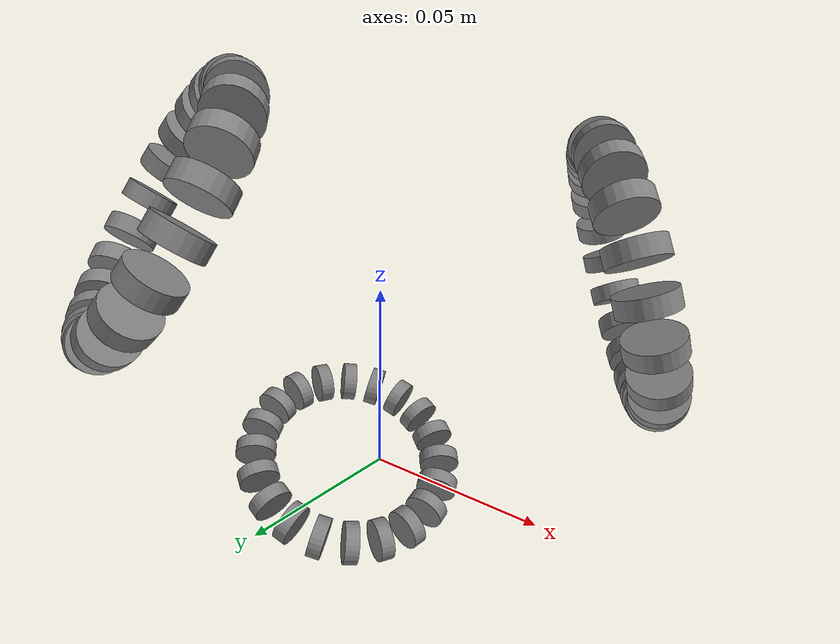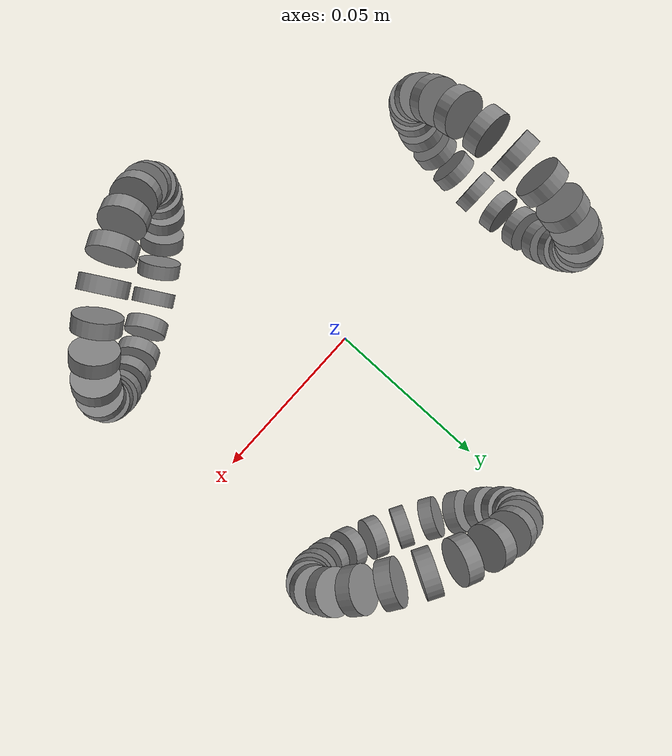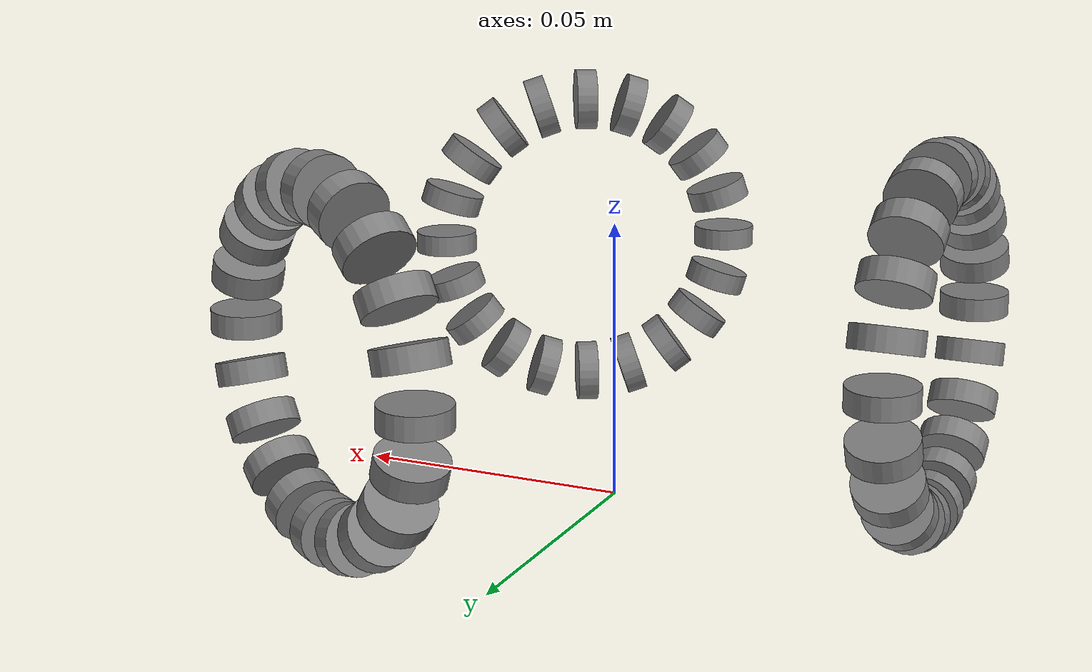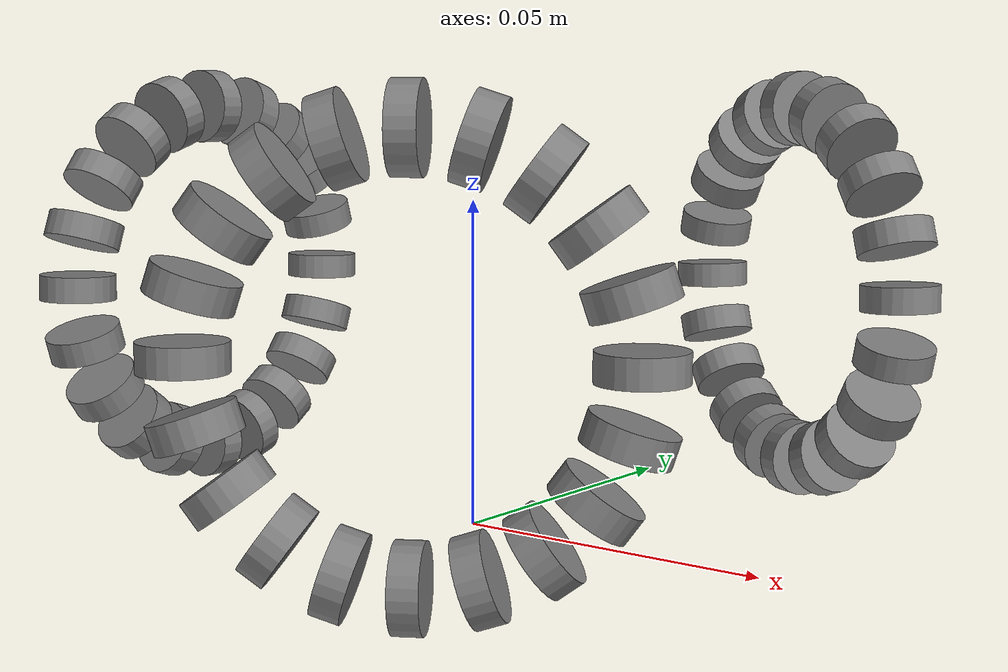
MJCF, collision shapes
<?xml version="1.0" ?>
<!-- Generated using onshape-to-robot -->
<!-- Onshape https://cad.onshape.com/documents/81e7adfaf4d8d74f2936fbd5/w/97141f458dee8c3b80cbf3d2/e/5e1ff591ff562de3da8ed2af -->
<mujoco model="rsk_mujoco">
  <compiler angle="radian" meshdir="assets" autolimits="true"/>
  <option noslip_iterations="1"/>
  <default>
    <default class="rsk_mujoco">
      <joint frictionloss="0.1" armature="0.005"/>
      <position kp="50" dampratio="1"/>
      <default class="visual">
        <geom type="mesh" contype="0" conaffinity="0" group="2"/>
      </default>
      <default class="collision">
        <geom group="3"/>
      </default>
    </default>
  </default>
  <worldbody>
    <!-- Link base -->
    <body name="base" pos="0 0 0" quat="1 0 0 0" childclass="rsk_mujoco">
      <freejoint name="base_freejoint"/>
      <inertial pos="0.00173842 -0.00175451 0.0439178" mass="0.374118" fullinertia="0.00052369 0.000556537 0.00084026 -1.32858e-05 3.13518e-05 1.1424e-05"/>
      <!-- Part m3_spacer__length_0_02_meter -->
      <geom type="mesh" class="visual" pos="0.0249812 -0.0237906 0.0511" quat="0.707107 2.5411e-21 -5.02926e-22 0.707107" mesh="m3_spacer__length_0_02_meter" material="m3_spacer__length_0_02_meter_material"/>
      <!-- Part 18650 -->
      <geom type="mesh" class="visual" pos="-0.022609 -0.0400272 0.0732537" quat="8.39142e-54 0.258819 0.965926 -4.84479e-54" mesh="18650" material="18650_material"/>
      <!-- Part hex_socket_head_cap_screw_m3x0_50_x_6__acf8a907a0472c0ae6086bf20401fa07 -->
      <geom type="mesh" class="visual" pos="0.0619875 -1.23093e-07 0.013" quat="0 0.707107 0.707107 0" mesh="hex_socket_head_cap_screw_m3x0_50_x_6__acf8a907a0472c0ae6086bf20401fa07" material="hex_socket_head_cap_screw_m3x0_50_x_6__acf8a907a0472c0ae6086bf20401fa07_material"/>
      <!-- Part marker -->
      <geom type="mesh" class="visual" pos="-1.25138e-05 -1.23093e-07 0.0681" quat="0.707107 3.38813e-21 -1.3483e-21 0.707107" mesh="marker" material="marker_material"/>
      <!-- Part hex_socket_head_cap_screw_m3x0_50_x_25_x_18__e477b94a6da3e3efbf1606183756b785 -->
      <geom type="mesh" class="visual" pos="0.00809374 -0.0335406 0.013" quat="0 0.707107 0.707107 0" mesh="hex_socket_head_cap_screw_m3x0_50_x_25_x_18__e477b94a6da3e3efbf1606183756b785" material="hex_socket_head_cap_screw_m3x0_50_x_25_x_18__e477b94a6da3e3efbf1606183756b785_material"/>
      <!-- Part hex_socket_head_cap_screw_m3x0_50_x_25_x_18__e477b94a6da3e3efbf1606183756b785_2 -->
      <geom type="mesh" class="visual" pos="-0.0331125 0.00974988 0.013" quat="0 0.707107 0.707107 0" mesh="hex_socket_head_cap_screw_m3x0_50_x_25_x_18__e477b94a6da3e3efbf1606183756b785" material="hex_socket_head_cap_screw_m3x0_50_x_25_x_18__e477b94a6da3e3efbf1606183756b785_material"/>
      <!-- Part hex_socket_head_cap_screw_m3x0_50_x_25_x_18__e477b94a6da3e3efbf1606183756b785_3 -->
      <geom type="mesh" class="visual" pos="0.0249812 0.0237903 0.013" quat="0 0.707107 0.707107 0" mesh="hex_socket_head_cap_screw_m3x0_50_x_25_x_18__e477b94a6da3e3efbf1606183756b785" material="hex_socket_head_cap_screw_m3x0_50_x_25_x_18__e477b94a6da3e3efbf1606183756b785_material"/>
      <!-- Part 18650_2 -->
      <geom type="mesh" class="visual" pos="-0.00915859 -0.0570304 0.0732537" quat="2.79714e-54 0.258819 0.965926 -1.61493e-54" mesh="18650" material="18650_material"/>
      <!-- Part m3_spacer__length_0_03_meter -->
      <geom type="mesh" class="visual" pos="-0.0723497 0.0332915 0.0176" quat="0.707107 0 0 0.707107" mesh="m3_spacer__length_0_03_meter" material="m3_spacer__length_0_03_meter_material"/>
      <!-- Part frame -->
      <geom type="mesh" class="visual" pos="-1.25138e-05 -1.23093e-07 0.0481" quat="0.707107 -0 1.11022e-16 0.707107" mesh="frame" material="frame_material"/>
      <!-- Part m3_spacer__length_0_006_meter -->
      <geom type="mesh" class="visual" pos="0.0249812 -0.0237906 0.0421" quat="0.5 0 0 0.866025" mesh="m3_spacer__length_0_006_meter" material="m3_spacer__length_0_006_meter_material"/>
      <!-- Part blue1_blue -->
      <geom type="mesh" class="visual" pos="0.000273519 0.00122933 0.0681" quat="0.707107 0 0 0.707107" mesh="blue1_blue" material="blue1_blue_material"/>
      <!-- Part hex_socket_head_cap_screw_m3x0_50_x_25_x_18__e477b94a6da3e3efbf1606183756b785_4 -->
      <geom type="mesh" class="visual" pos="0.00809374 0.0335403 0.013" quat="0 0.707107 0.707107 0" mesh="hex_socket_head_cap_screw_m3x0_50_x_25_x_18__e477b94a6da3e3efbf1606183756b785" material="hex_socket_head_cap_screw_m3x0_50_x_25_x_18__e477b94a6da3e3efbf1606183756b785_material"/>
      <!-- Part coupler -->
      <geom type="mesh" class="visual" pos="0.0329448 0.015656 0.0511" quat="0.258819 0 -2.22045e-16 0.965926" mesh="coupler" material="coupler_material"/>
      <!-- Part hex_socket_head_cap_screw_m3x0_50_x_6__acf8a907a0472c0ae6086bf20401fa07_2 -->
      <geom type="mesh" class="visual" pos="0.0474875 -1.23093e-07 0.013" quat="0 0.707107 0.707107 0" mesh="hex_socket_head_cap_screw_m3x0_50_x_6__acf8a907a0472c0ae6086bf20401fa07" material="hex_socket_head_cap_screw_m3x0_50_x_6__acf8a907a0472c0ae6086bf20401fa07_material"/>
      <!-- Part blue1_white -->
      <geom type="mesh" class="visual" pos="-1.02871e-05 -1.23093e-07 0.0829" quat="1.3188e-25 -0.707107 0.707107 -1.8866e-24" mesh="blue1_white" material="blue1_white_material"/>
      <!-- Part hex_socket_head_cap_screw_m3x0_50_x_25_x_18__e477b94a6da3e3efbf1606183756b785_5 -->
      <geom type="mesh" class="visual" pos="0.0249812 -0.0237906 0.013" quat="0 0.707107 0.707107 0" mesh="hex_socket_head_cap_screw_m3x0_50_x_25_x_18__e477b94a6da3e3efbf1606183756b785" material="hex_socket_head_cap_screw_m3x0_50_x_25_x_18__e477b94a6da3e3efbf1606183756b785_material"/>
      <!-- Part board -->
      <geom type="mesh" class="visual" pos="-1.25138e-05 -1.23093e-07 0.0176" quat="0.707107 0 0 0.707107" mesh="board" material="board_material"/>
      <!-- Part hex_socket_head_cap_screw_m3x0_50_x_25_x_18__e477b94a6da3e3efbf1606183756b785_6 -->
      <geom type="mesh" class="visual" pos="-0.0331125 -0.00975012 0.013" quat="0 0.707107 0.707107 0" mesh="hex_socket_head_cap_screw_m3x0_50_x_25_x_18__e477b94a6da3e3efbf1606183756b785" material="hex_socket_head_cap_screw_m3x0_50_x_25_x_18__e477b94a6da3e3efbf1606183756b785_material"/>
      <!-- Part coil -->
      <geom type="mesh" class="visual" pos="0.0694875 -0.00660012 0.0176" quat="0.707107 0 -0.707107 0" mesh="coil" material="coil_material"/>
      <!-- Part frame_2 -->
      <geom type="mesh" class="visual" pos="0.0694875 -0.00660012 0.0176" quat="0.707107 0 -0.707107 0" mesh="frame__2" material="frame__2_material"/>
      <!-- Part n20 -->
      <geom type="mesh" class="visual" pos="-0.0166125 -0.00600012 0.0296" quat="0.707107 0 0 0.707107" mesh="n20" material="n20_material"/>
      <!-- Part motorbox_top -->
      <geom type="mesh" class="visual" pos="-0.0166125 -0.00600012 0.0296" quat="0.707107 0 0 0.707107" mesh="motorbox_top" material="motorbox_top_material"/>
      <!-- Part motorbox_bottom -->
      <geom type="mesh" class="visual" pos="-0.0166125 -0.00600012 0.0296" quat="0.707107 0 0 0.707107" mesh="motorbox_bottom" material="motorbox_bottom_material"/>
      <!-- Part n20_2 -->
      <geom type="mesh" class="visual" pos="0.0134836 -0.0113761 0.0296" quat="0.258819 0 0 -0.965926" mesh="n20" material="n20_material"/>
      <!-- Part motorbox_top_2 -->
      <geom type="mesh" class="visual" pos="0.0134836 -0.0113761 0.0296" quat="0.258819 0 0 -0.965926" mesh="motorbox_top" material="motorbox_top_material"/>
      <!-- Part motorbox_bottom_2 -->
      <geom type="mesh" class="visual" pos="0.0134836 -0.0113761 0.0296" quat="0.258819 0 0 -0.965926" mesh="motorbox_bottom" material="motorbox_bottom_material"/>
      <!-- Part m3_spacer__length_0_03_meter_2 -->
      <geom type="mesh" class="visual" pos="0.00732465 -0.0792918 0.0176" quat="0.707107 0 0 0.707107" mesh="m3_spacer__length_0_03_meter" material="m3_spacer__length_0_03_meter_material"/>
      <!-- Part m3_spacer__length_0_03_meter_3 -->
      <geom type="mesh" class="visual" pos="-0.0534311 0.0465236 0.0176" quat="0.707107 0 0 0.707107" mesh="m3_spacer__length_0_03_meter" material="m3_spacer__length_0_03_meter_material"/>
      <!-- Part m3_spacer__length_0_03_meter_4 -->
      <geom type="mesh" class="visual" pos="0.0649875 0.0459999 0.0176" quat="0.707107 0 0 0.707107" mesh="m3_spacer__length_0_03_meter" material="m3_spacer__length_0_03_meter_material"/>
      <!-- Part m3_spacer__length_0_03_meter_5 -->
      <geom type="mesh" class="visual" pos="-0.0135939 -0.0695238 0.0176" quat="0.707107 0 0 0.707107" mesh="m3_spacer__length_0_03_meter" material="m3_spacer__length_0_03_meter_material"/>
      <!-- Part m3_spacer__length_0_03_meter_6 -->
      <geom type="mesh" class="visual" pos="-0.0723497 -0.0332918 0.0176" quat="0.707107 0 0 0.707107" mesh="m3_spacer__length_0_03_meter" material="m3_spacer__length_0_03_meter_material"/>
      <!-- Part m3_spacer__length_0_03_meter_7 -->
      <geom type="mesh" class="visual" pos="-0.0534311 -0.0465238 0.0176" quat="0.707107 0 0 0.707107" mesh="m3_spacer__length_0_03_meter" material="m3_spacer__length_0_03_meter_material"/>
      <!-- Part m3_spacer__length_0_03_meter_8 -->
      <geom type="mesh" class="visual" pos="0.0649875 -0.0460001 0.0176" quat="0.707107 0 0 0.707107" mesh="m3_spacer__length_0_03_meter" material="m3_spacer__length_0_03_meter_material"/>
      <!-- Part m3_spacer__length_0_03_meter_9 -->
      <geom type="mesh" class="visual" pos="0.00732465 0.0792915 0.0176" quat="0.707107 0 0 0.707107" mesh="m3_spacer__length_0_03_meter" material="m3_spacer__length_0_03_meter_material"/>
      <!-- Part m3_spacer__length_0_03_meter_10 -->
      <geom type="mesh" class="visual" pos="-0.0135939 0.0695236 0.0176" quat="0.707107 0 0 0.707107" mesh="m3_spacer__length_0_03_meter" material="m3_spacer__length_0_03_meter_material"/>
      <!-- Part m3_spacer__length_0_02_meter_2 -->
      <geom type="mesh" class="visual" pos="0.00809374 0.0335403 0.0511" quat="0.707107 2.5411e-21 -5.02926e-22 0.707107" mesh="m3_spacer__length_0_02_meter" material="m3_spacer__length_0_02_meter_material"/>
      <!-- Part m3_spacer__length_0_02_meter_3 -->
      <geom type="mesh" class="visual" pos="-0.0331125 -0.00975012 0.0511" quat="0.707107 2.5411e-21 -5.02926e-22 0.707107" mesh="m3_spacer__length_0_02_meter" material="m3_spacer__length_0_02_meter_material"/>
      <!-- Part m3_spacer__length_0_02_meter_4 -->
      <geom type="mesh" class="visual" pos="0.0249812 0.0237903 0.0511" quat="0.707107 2.5411e-21 -5.02926e-22 0.707107" mesh="m3_spacer__length_0_02_meter" material="m3_spacer__length_0_02_meter_material"/>
      <!-- Part m3_spacer__length_0_02_meter_5 -->
      <geom type="mesh" class="visual" pos="-0.0331125 0.00974988 0.0511" quat="0.707107 2.5411e-21 -5.02926e-22 0.707107" mesh="m3_spacer__length_0_02_meter" material="m3_spacer__length_0_02_meter_material"/>
      <!-- Part m3_spacer__length_0_02_meter_6 -->
      <geom type="mesh" class="visual" pos="0.00809374 -0.0335406 0.0511" quat="0.707107 2.5411e-21 -5.02926e-22 0.707107" mesh="m3_spacer__length_0_02_meter" material="m3_spacer__length_0_02_meter_material"/>
      <!-- Part m3_spacer__length_0_006_meter_2 -->
      <geom type="mesh" class="visual" pos="0.00809374 -0.0335406 0.0421" quat="0.5 0 0 0.866025" mesh="m3_spacer__length_0_006_meter" material="m3_spacer__length_0_006_meter_material"/>
      <!-- Part m3_spacer__length_0_006_meter_3 -->
      <geom type="mesh" class="visual" pos="0.0249812 0.0237903 0.0421" quat="0.5 0 0 -0.866025" mesh="m3_spacer__length_0_006_meter" material="m3_spacer__length_0_006_meter_material"/>
      <!-- Part m3_spacer__length_0_006_meter_4 -->
      <geom type="mesh" class="visual" pos="-0.0331125 0.00974988 0.0421" quat="1 0 0 -2.498e-16" mesh="m3_spacer__length_0_006_meter" material="m3_spacer__length_0_006_meter_material"/>
      <!-- Part m3_spacer__length_0_006_meter_5 -->
      <geom type="mesh" class="visual" pos="0.00809374 0.0335403 0.0421" quat="0.5 0 0 -0.866025" mesh="m3_spacer__length_0_006_meter" material="m3_spacer__length_0_006_meter_material"/>
      <!-- Part m3_spacer__length_0_006_meter_6 -->
      <geom type="mesh" class="visual" pos="-0.0331125 -0.00975012 0.0421" quat="1 0 0 -2.498e-16" mesh="m3_spacer__length_0_006_meter" material="m3_spacer__length_0_006_meter_material"/>
      <!-- Part n20_3 -->
      <geom type="mesh" class="visual" pos="0.00309133 0.0173759 0.0296" quat="0.965926 0 0 -0.258819" mesh="n20" material="n20_material"/>
      <!-- Part motorbox_top_3 -->
      <geom type="mesh" class="visual" pos="0.00309133 0.0173759 0.0296" quat="0.965926 0 0 -0.258819" mesh="motorbox_top" material="motorbox_top_material"/>
      <!-- Part motorbox_bottom_3 -->
      <geom type="mesh" class="visual" pos="0.00309133 0.0173759 0.0296" quat="0.965926 0 0 -0.258819" mesh="motorbox_bottom" material="motorbox_bottom_material"/>
      <!-- Link wheel_no_passives -->
      <body name="wheel_no_passives" pos="0.0235875 0.0408763 0.0346" quat="0.704604 0.639927 -0.300821 -0.0594445">
        <!-- Joint from base to wheel_no_passives -->
        <joint name="wheel1_speed" type="hinge"/>
        <inertial pos="6.58074e-07 -5.13421e-06 -0.00986839" mass="0.0266331" fullinertia="3.77181e-06 3.77247e-06 7.07069e-06 8.61773e-10 -7.42627e-10 -1.53938e-11"/>
        <!-- Part wheel2 -->
        <geom type="mesh" class="visual" pos="1.38778e-17 -6.93889e-18 -0.0075" quat="2.77556e-17 2.77556e-17 1 -2.77556e-17" mesh="wheel2" material="wheel2_material"/>
        <!-- Part hex_nut_style_1_grade_a___b_m3x0_5__59e06dee1671df03e56ade283ea1f5ec -->
        <geom type="mesh" class="visual" pos="-3.46945e-18 0.008 -0.0132" quat="4.92914e-17 -0.707107 0.707107 -5.83907e-17" mesh="hex_nut_style_1_grade_a___b_m3x0_5__59e06dee1671df03e56ade283ea1f5ec" material="hex_nut_style_1_grade_a___b_m3x0_5__59e06dee1671df03e56ade283ea1f5ec_material"/>
        <!-- Part coupler_2 -->
        <geom type="mesh" class="visual" pos="6.93889e-18 0 -0.012" quat="1 -0 -0 -1.11022e-16" mesh="coupler__2" material="coupler__2_material"/>
        <!-- Part hex_socket_head_cap_screw_m3x0_50_x_8__cca8b3192bff7455e4b9cc3364d29e0e -->
        <geom type="mesh" class="visual" pos="2.77556e-17 0.008 -0.005" quat="1.11022e-16 0 -1.11022e-16 1" mesh="hex_socket_head_cap_screw_m3x0_50_x_8__cca8b3192bff7455e4b9cc3364d29e0e" material="hex_socket_head_cap_screw_m3x0_50_x_8__cca8b3192bff7455e4b9cc3364d29e0e_material"/>
        <!-- Part hex_socket_head_cap_screw_m3x0_50_x_8__cca8b3192bff7455e4b9cc3364d29e0e_2 -->
        <geom type="mesh" class="visual" pos="-0.0138564 0.008 -0.005" quat="5.20417e-17 0 1.11022e-16 1" mesh="hex_socket_head_cap_screw_m3x0_50_x_8__cca8b3192bff7455e4b9cc3364d29e0e" material="hex_socket_head_cap_screw_m3x0_50_x_8__cca8b3192bff7455e4b9cc3364d29e0e_material"/>
        <!-- Part wheel1 -->
        <geom type="mesh" class="visual" pos="1.38778e-17 -6.93889e-18 -0.0075" quat="2.77556e-17 2.77556e-17 1 -2.77556e-17" mesh="wheel1" material="wheel1_material"/>
        <!-- Part hex_nut_style_1_grade_a___b_m3x0_5__59e06dee1671df03e56ade283ea1f5ec_2 -->
        <geom type="mesh" class="visual" pos="-0.0138564 0.008 -0.0142" quat="0.965926 -2.39044e-17 -1.94289e-16 -0.258819" mesh="hex_nut_style_1_grade_a___b_m3x0_5__59e06dee1671df03e56ade283ea1f5ec" material="hex_nut_style_1_grade_a___b_m3x0_5__59e06dee1671df03e56ade283ea1f5ec_material"/>
        <!-- Part hex_nut_style_1_grade_a___b_m3x0_5__59e06dee1671df03e56ade283ea1f5ec_3 -->
        <geom type="mesh" class="visual" pos="0.0138564 -0.008 -0.0142" quat="0.258819 1.18259e-16 3.33067e-16 0.965926" mesh="hex_nut_style_1_grade_a___b_m3x0_5__59e06dee1671df03e56ade283ea1f5ec" material="hex_nut_style_1_grade_a___b_m3x0_5__59e06dee1671df03e56ade283ea1f5ec_material"/>
        <!-- Part hex_nut_style_1_grade_a___b_m3x0_5__59e06dee1671df03e56ade283ea1f5ec_4 -->
        <geom type="mesh" class="visual" pos="1.04083e-17 -0.016 -0.0142" quat="0.707107 -9.47361e-17 1.11022e-16 0.707107" mesh="hex_nut_style_1_grade_a___b_m3x0_5__59e06dee1671df03e56ade283ea1f5ec" material="hex_nut_style_1_grade_a___b_m3x0_5__59e06dee1671df03e56ade283ea1f5ec_material"/>
        <!-- Part hex_socket_head_cap_screw_m3x0_50_x_8__cca8b3192bff7455e4b9cc3364d29e0e_3 -->
        <geom type="mesh" class="visual" pos="0.0138564 -0.008 -0.005" quat="1 1.64464e-16 -0 3.33067e-16" mesh="hex_socket_head_cap_screw_m3x0_50_x_8__cca8b3192bff7455e4b9cc3364d29e0e" material="hex_socket_head_cap_screw_m3x0_50_x_8__cca8b3192bff7455e4b9cc3364d29e0e_material"/>
        <!-- Part hex_nut_style_1_grade_a___b_m3x0_5__59e06dee1671df03e56ade283ea1f5ec_5 -->
        <geom type="mesh" class="visual" pos="-0.0138564 -0.008 -0.0142" quat="0.965926 4.93526e-17 2.22045e-16 0.258819" mesh="hex_nut_style_1_grade_a___b_m3x0_5__59e06dee1671df03e56ade283ea1f5ec" material="hex_nut_style_1_grade_a___b_m3x0_5__59e06dee1671df03e56ade283ea1f5ec_material"/>
        <!-- Part hex_socket_head_cap_screw_m3x0_50_x_8__cca8b3192bff7455e4b9cc3364d29e0e_4 -->
        <geom type="mesh" class="visual" pos="-0.0138564 -0.008 -0.005" quat="0.5 -1.44896e-16 -5.55112e-17 -0.866025" mesh="hex_socket_head_cap_screw_m3x0_50_x_8__cca8b3192bff7455e4b9cc3364d29e0e" material="hex_socket_head_cap_screw_m3x0_50_x_8__cca8b3192bff7455e4b9cc3364d29e0e_material"/>
        <!-- Part hex_socket_head_cap_screw_m3x0_50_x_8__cca8b3192bff7455e4b9cc3364d29e0e_5 -->
        <geom type="mesh" class="visual" pos="0.0138564 0.008 -0.005" quat="0.866025 2.3143e-17 2.22045e-16 0.5" mesh="hex_socket_head_cap_screw_m3x0_50_x_8__cca8b3192bff7455e4b9cc3364d29e0e" material="hex_socket_head_cap_screw_m3x0_50_x_8__cca8b3192bff7455e4b9cc3364d29e0e_material"/>
        <!-- Part hex_socket_head_cap_screw_m3x0_50_x_8__cca8b3192bff7455e4b9cc3364d29e0e_6 -->
        <geom type="mesh" class="visual" pos="7.45931e-17 -0.016 -0.005" quat="0.866025 -1.82562e-17 5.55112e-17 -0.5" mesh="hex_socket_head_cap_screw_m3x0_50_x_8__cca8b3192bff7455e4b9cc3364d29e0e" material="hex_socket_head_cap_screw_m3x0_50_x_8__cca8b3192bff7455e4b9cc3364d29e0e_material"/>
        <!-- Part hex_nut_style_1_grade_a___b_m3x0_5__59e06dee1671df03e56ade283ea1f5ec_6 -->
        <geom type="mesh" class="visual" pos="0.0138564 0.008 -0.0142" quat="0.258819 -6.60024e-17 2.77556e-16 -0.965926" mesh="hex_nut_style_1_grade_a___b_m3x0_5__59e06dee1671df03e56ade283ea1f5ec" material="hex_nut_style_1_grade_a___b_m3x0_5__59e06dee1671df03e56ade283ea1f5ec_material"/>
        <!-- Part hex_nut_style_1_grade_a___b_m3x0_5__59e06dee1671df03e56ade283ea1f5ec_7 -->
        <geom type="mesh" class="visual" pos="-5.89806e-17 0.016 -0.0142" quat="0.707107 1.03976e-17 2.77556e-17 -0.707107" mesh="hex_nut_style_1_grade_a___b_m3x0_5__59e06dee1671df03e56ade283ea1f5ec" material="hex_nut_style_1_grade_a___b_m3x0_5__59e06dee1671df03e56ade283ea1f5ec_material"/>
        <!-- Part hex_socket_head_cap_screw_m3x0_50_x_8__cca8b3192bff7455e4b9cc3364d29e0e_7 -->
        <geom type="mesh" class="visual" pos="-2.25514e-17 0.016 -0.005" quat="0.5 6.56714e-17 -1.11022e-16 0.866025" mesh="hex_socket_head_cap_screw_m3x0_50_x_8__cca8b3192bff7455e4b9cc3364d29e0e" material="hex_socket_head_cap_screw_m3x0_50_x_8__cca8b3192bff7455e4b9cc3364d29e0e_material"/>
        <!-- Part hex_nut_style_1_grade_a___b_m3x0_5__59e06dee1671df03e56ade283ea1f5ec_8 -->
        <geom type="mesh" class="visual" pos="0.008 -2.08167e-17 -0.0132" quat="8.32667e-17 1.16746e-16 1 -2.77556e-17" mesh="hex_nut_style_1_grade_a___b_m3x0_5__59e06dee1671df03e56ade283ea1f5ec" material="hex_nut_style_1_grade_a___b_m3x0_5__59e06dee1671df03e56ade283ea1f5ec_material"/>
        <!-- Part hex_nut_style_1_grade_a___b_m3x0_5__59e06dee1671df03e56ade283ea1f5ec_9 -->
        <geom type="mesh" class="visual" pos="-5.89806e-17 -0.008 -0.0132" quat="4.15299e-17 0.707107 0.707107 -1.32748e-16" mesh="hex_nut_style_1_grade_a___b_m3x0_5__59e06dee1671df03e56ade283ea1f5ec" material="hex_nut_style_1_grade_a___b_m3x0_5__59e06dee1671df03e56ade283ea1f5ec_material"/>
        <!-- Part hex_socket_head_cap_screw_m3x0_50_x_8__cca8b3192bff7455e4b9cc3364d29e0e_8 -->
        <geom type="mesh" class="visual" pos="-0.008 -4.85723e-17 -0.005" quat="0.707107 -0 -2.22045e-16 -0.707107" mesh="hex_socket_head_cap_screw_m3x0_50_x_8__cca8b3192bff7455e4b9cc3364d29e0e" material="hex_socket_head_cap_screw_m3x0_50_x_8__cca8b3192bff7455e4b9cc3364d29e0e_material"/>
        <!-- Part hex_socket_head_cap_screw_m3x0_50_x_8__cca8b3192bff7455e4b9cc3364d29e0e_9 -->
        <geom type="mesh" class="visual" pos="-5.89806e-17 -0.008 -0.005" quat="1 -1.36726e-16 1.11022e-16 -1.11022e-16" mesh="hex_socket_head_cap_screw_m3x0_50_x_8__cca8b3192bff7455e4b9cc3364d29e0e" material="hex_socket_head_cap_screw_m3x0_50_x_8__cca8b3192bff7455e4b9cc3364d29e0e_material"/>
        <!-- Part hex_nut_style_1_grade_a___b_m3x0_5__59e06dee1671df03e56ade283ea1f5ec_10 -->
        <geom type="mesh" class="visual" pos="-0.008 -6.93889e-18 -0.0132" quat="9.78383e-19 1 -2.38694e-17 7.39632e-17" mesh="hex_nut_style_1_grade_a___b_m3x0_5__59e06dee1671df03e56ade283ea1f5ec" material="hex_nut_style_1_grade_a___b_m3x0_5__59e06dee1671df03e56ade283ea1f5ec_material"/>
        <!-- Part hex_socket_head_cap_screw_m3x0_50_x_8__cca8b3192bff7455e4b9cc3364d29e0e_10 -->
        <geom type="mesh" class="visual" pos="0.008 -3.46945e-17 -0.005" quat="0.707107 0 0 0.707107" mesh="hex_socket_head_cap_screw_m3x0_50_x_8__cca8b3192bff7455e4b9cc3364d29e0e" material="hex_socket_head_cap_screw_m3x0_50_x_8__cca8b3192bff7455e4b9cc3364d29e0e_material"/>
        <!-- Link pin_bearing_oring -->
        <body name="pin_bearing_oring" pos="-0.00880698 0.0271051 -0.01" quat="0.698401 0.110616 -0.698401 0.110616">
          <!-- Joint from wheel_no_passives to pin_bearing_oring -->
          <joint name="wheel1_passive_1" type="hinge"/>
          <inertial pos="-3.87818e-17 7.8919e-17 -6.24755e-17" mass="0.00337198" fullinertia="3.55777e-08 3.55777e-08 6.05554e-08 4.45528e-24 4.81239e-24 2.99289e-24"/>
          <!-- Part oring -->
          <geom type="mesh" class="visual" pos="-4.16334e-17 9.02056e-17 0.002" quat="0 1 0 0" mesh="oring" material="oring_material"/>
          <!-- Part pin -->
          <geom type="mesh" class="visual" pos="-1.38778e-17 -6.93889e-18 0.0035" quat="0 1 0 0" mesh="pin" material="pin_material"/>
          <!-- Part bearing -->
          <geom class="collision" pos="-4.17181e-17 9.00576e-17 -7.11237e-17" quat="0 1 0 0" type="cylinder" size="0.006 0.002"/>
          <geom type="mesh" class="visual" pos="-4.16334e-17 9.02056e-17 0.002" quat="0 1 0 0" mesh="bearing" material="bearing_material"/>
        </body>
        <!-- Link pin_bearing_oring_2 -->
        <body name="pin_bearing_oring_2" pos="-0.0167519 0.023057 -0.01" quat="0.630037 -0.630037 0.32102 -0.32102">
          <!-- Joint from wheel_no_passives to pin_bearing_oring_2 -->
          <joint name="wheel1_passive_2" type="hinge"/>
          <inertial pos="-6.83058e-18 5.43947e-17 -1.3379e-16" mass="0.00337198" fullinertia="3.55777e-08 3.55777e-08 6.05554e-08 -1.18088e-25 -7.1728e-24 4.02232e-25"/>
          <!-- Part oring_2 -->
          <geom type="mesh" class="visual" pos="-6.93889e-18 6.245e-17 0.002" quat="0 1 0 0" mesh="oring" material="oring_material"/>
          <!-- Part pin_2 -->
          <geom type="mesh" class="visual" pos="-6.93889e-18 -6.93889e-18 0.0035" quat="0 1 0 0" mesh="pin" material="pin_material"/>
          <!-- Part bearing_2 -->
          <geom class="collision" pos="-6.70839e-18 6.24373e-17 -1.50921e-16" quat="0 1 0 0" type="cylinder" size="0.006 0.002"/>
          <geom type="mesh" class="visual" pos="-6.93889e-18 6.245e-17 0.002" quat="0 1 0 0" mesh="bearing" material="bearing_material"/>
        </body>
        <!-- Link pin_bearing_oring_3 -->
        <body name="pin_bearing_oring_3" pos="-0.023057 0.0167519 -0.01" quat="0.672499 0.672499 -0.218508 -0.218508">
          <!-- Joint from wheel_no_passives to pin_bearing_oring_3 -->
          <joint name="wheel1_passive_3" type="hinge"/>
          <inertial pos="6.80356e-17 9.30254e-17 8.88331e-17" mass="0.00337198" fullinertia="3.55777e-08 3.55777e-08 6.05554e-08 -5.07525e-24 -6.51667e-24 -8.8806e-24"/>
          <!-- Part oring_3 -->
          <geom type="mesh" class="visual" pos="7.63278e-17 1.04083e-16 -0.002" quat="1 -1.18551e-16 3.33067e-16 1.66533e-16" mesh="oring" material="oring_material"/>
          <!-- Part pin_3 -->
          <geom type="mesh" class="visual" pos="0 0 -0.0035" quat="1 -1.18551e-16 3.33067e-16 1.66533e-16" mesh="pin" material="pin_material"/>
          <!-- Part bearing_3 -->
          <geom class="collision" pos="7.66345e-17 1.0425e-16 9.93129e-17" quat="1 -1.18551e-16 3.33067e-16 1.66533e-16" type="cylinder" size="0.006 0.002"/>
          <geom type="mesh" class="visual" pos="7.63278e-17 1.04083e-16 -0.002" quat="1 -1.18551e-16 3.33067e-16 1.66533e-16" mesh="bearing" material="bearing_material"/>
        </body>
        <!-- Link pin_bearing_oring_4 -->
        <body name="pin_bearing_oring_4" pos="-0.0271051 0.00880698 -0.01" quat="0.698401 0.698401 -0.110616 -0.110616">
          <!-- Joint from wheel_no_passives to pin_bearing_oring_4 -->
          <joint name="wheel1_passive_4" type="hinge"/>
          <inertial pos="-2.4811e-17 -1.95948e-17 -1.33742e-16" mass="0.00337198" fullinertia="3.55777e-08 3.55777e-08 6.05554e-08 -8.31745e-24 1.55915e-26 2.25747e-26"/>
          <!-- Part oring_4 -->
          <geom type="mesh" class="visual" pos="-2.77556e-17 -2.08167e-17 0.002" quat="0 1 0 0" mesh="oring" material="oring_material"/>
          <!-- Part pin_4 -->
          <geom type="mesh" class="visual" pos="0 -6.93889e-18 0.0035" quat="0 1 0 0" mesh="pin" material="pin_material"/>
          <!-- Part bearing_4 -->
          <geom class="collision" pos="-2.77544e-17 -2.08082e-17 -1.50487e-16" quat="0 1 0 0" type="cylinder" size="0.006 0.002"/>
          <geom type="mesh" class="visual" pos="-2.77556e-17 -2.08167e-17 0.002" quat="0 1 0 0" mesh="bearing" material="bearing_material"/>
        </body>
        <!-- Link pin_bearing_oring_5 -->
        <body name="pin_bearing_oring_5" pos="-0.0285 0 -0.01" quat="0.707107 0.707107 -2.4647e-14 2.44565e-14">
          <!-- Joint from wheel_no_passives to pin_bearing_oring_5 -->
          <joint name="wheel1_passive_5" type="hinge"/>
          <inertial pos="9.8618e-17 1.9702e-16 -7.28838e-17" mass="0.00337198" fullinertia="3.55777e-08 3.55777e-08 6.05554e-08 4.34965e-24 -3.71291e-24 -1.32107e-25"/>
          <!-- Part oring_5 -->
          <geom type="mesh" class="visual" pos="1.11022e-16 2.22045e-16 0.002" quat="0 1 0 0" mesh="oring" material="oring_material"/>
          <!-- Part pin_5 -->
          <geom type="mesh" class="visual" pos="0 0 0.0035" quat="0 1 0 0" mesh="pin" material="pin_material"/>
          <!-- Part bearing_5 -->
          <geom class="collision" pos="1.11093e-16 2.22029e-16 -8.1532e-17" quat="0 1 0 0" type="cylinder" size="0.006 0.002"/>
          <geom type="mesh" class="visual" pos="1.11022e-16 2.22045e-16 0.002" quat="0 1 0 0" mesh="bearing" material="bearing_material"/>
        </body>
        <!-- Link pin_bearing_oring_6 -->
        <body name="pin_bearing_oring_6" pos="-0.0271051 -0.00880698 -0.01" quat="0.698401 0.698401 0.110616 0.110616">
          <!-- Joint from wheel_no_passives to pin_bearing_oring_6 -->
          <joint name="wheel1_passive_6" type="hinge"/>
          <inertial pos="-3.84923e-17 1.25249e-17 7.95334e-17" mass="0.00337198" fullinertia="3.55777e-08 3.55777e-08 6.05554e-08 -6.29234e-24 -2.83276e-23 -2.65958e-23"/>
          <!-- Part oring_6 -->
          <geom type="mesh" class="visual" pos="-4.25007e-17 1.38778e-17 -0.002" quat="1 -1.99037e-16 1.11022e-16 -2.77556e-16" mesh="oring" material="oring_material"/>
          <!-- Part pin_6 -->
          <geom type="mesh" class="visual" pos="-8.67362e-19 0 -0.0035" quat="1 -1.99037e-16 1.11022e-16 -2.77556e-16" mesh="pin" material="pin_material"/>
          <!-- Part bearing_6 -->
          <geom class="collision" pos="-4.29413e-17 1.37484e-17 8.89046e-17" quat="1 -1.99037e-16 1.11022e-16 -2.77556e-16" type="cylinder" size="0.006 0.002"/>
          <geom type="mesh" class="visual" pos="-4.25007e-17 1.38778e-17 -0.002" quat="1 -1.99037e-16 1.11022e-16 -2.77556e-16" mesh="bearing" material="bearing_material"/>
        </body>
        <!-- Link pin_bearing_oring_7 -->
        <body name="pin_bearing_oring_7" pos="-0.023057 -0.0167519 -0.01" quat="0.672499 0.672499 0.218508 0.218508">
          <!-- Joint from wheel_no_passives to pin_bearing_oring_7 -->
          <joint name="wheel1_passive_7" type="hinge"/>
          <inertial pos="-1.7135e-17 -7.52272e-17 -8.70982e-17" mass="0.00337198" fullinertia="3.55777e-08 3.55777e-08 6.05554e-08 -1.49658e-24 -4.86468e-24 3.18491e-24"/>
          <!-- Part oring_7 -->
          <geom type="mesh" class="visual" pos="-1.91904e-17 -8.32667e-17 0.002" quat="0 1 0 0" mesh="oring" material="oring_material"/>
          <!-- Part pin_7 -->
          <geom type="mesh" class="visual" pos="-1.24683e-18 -6.93889e-18 0.0035" quat="0 1 0 0" mesh="pin" material="pin_material"/>
          <!-- Part bearing_7 -->
          <geom class="collision" pos="-1.90034e-17 -8.33718e-17 -9.84456e-17" quat="0 1 0 0" type="cylinder" size="0.006 0.002"/>
          <geom type="mesh" class="visual" pos="-1.91904e-17 -8.32667e-17 0.002" quat="0 1 0 0" mesh="bearing" material="bearing_material"/>
        </body>
        <!-- Link pin_bearing_oring_8 -->
        <body name="pin_bearing_oring_8" pos="-0.0167519 -0.023057 -0.01" quat="0.630037 0.630037 0.32102 0.32102">
          <!-- Joint from wheel_no_passives to pin_bearing_oring_8 -->
          <joint name="wheel1_passive_8" type="hinge"/>
          <inertial pos="2.02674e-18 -6.75099e-17 -7.51001e-17" mass="0.00337198" fullinertia="3.55777e-08 3.55777e-08 6.05554e-08 2.25894e-24 -5.19735e-25 5.59756e-24"/>
          <!-- Part oring_8 -->
          <geom type="mesh" class="visual" pos="2.60209e-18 -7.63278e-17 0.002" quat="0 1 0 0" mesh="oring" material="oring_material"/>
          <!-- Part pin_8 -->
          <geom type="mesh" class="visual" pos="-8.67362e-19 6.93889e-18 0.0035" quat="0 1 0 0" mesh="pin" material="pin_material"/>
          <!-- Part bearing_8 -->
          <geom class="collision" pos="2.55746e-18 -7.64263e-17 -8.50015e-17" quat="0 1 0 0" type="cylinder" size="0.006 0.002"/>
          <geom type="mesh" class="visual" pos="2.60209e-18 -7.63278e-17 0.002" quat="0 1 0 0" mesh="bearing" material="bearing_material"/>
        </body>
        <!-- Link pin_bearing_oring_9 -->
        <body name="pin_bearing_oring_9" pos="-0.00880698 -0.0271051 -0.01" quat="0.698401 -0.110616 -0.698401 -0.110616">
          <!-- Joint from wheel_no_passives to pin_bearing_oring_9 -->
          <joint name="wheel1_passive_9" type="hinge"/>
          <inertial pos="4.94255e-17 -8.04043e-17 -8.70983e-17" mass="0.00337198" fullinertia="3.55777e-08 3.55777e-08 6.05554e-08 -4.19431e-26 -6.12263e-24 -2.72239e-25"/>
          <!-- Part oring_9 -->
          <geom type="mesh" class="visual" pos="5.55112e-17 -9.02056e-17 0.002" quat="0 1 0 0" mesh="oring" material="oring_material"/>
          <!-- Part pin_9 -->
          <geom type="mesh" class="visual" pos="0 8.67362e-19 0.0035" quat="0 1 0 0" mesh="pin" material="pin_material"/>
          <!-- Part bearing_9 -->
          <geom class="collision" pos="5.57191e-17 -9.01972e-17 -9.80119e-17" quat="0 1 0 0" type="cylinder" size="0.006 0.002"/>
          <geom type="mesh" class="visual" pos="5.55112e-17 -9.02056e-17 0.002" quat="0 1 0 0" mesh="bearing" material="bearing_material"/>
        </body>
        <!-- Link pin_bearing_oring_10 -->
        <body name="pin_bearing_oring_10" pos="1.73472e-18 -0.0285 -0.01" quat="0.5 0.5 0.5 0.5">
          <!-- Joint from wheel_no_passives to pin_bearing_oring_10 -->
          <joint name="wheel1_passive_10" type="hinge"/>
          <inertial pos="2.13331e-17 6.12085e-17 3.94429e-17" mass="0.00337198" fullinertia="3.55777e-08 3.55777e-08 6.05554e-08 1.49973e-23 1.16808e-23 -7.60225e-24"/>
          <!-- Part oring_10 -->
          <geom type="mesh" class="visual" pos="2.42861e-17 6.93889e-17 -0.002" quat="1 -4.50019e-17 -2.22045e-16 2.77556e-17" mesh="oring" material="oring_material"/>
          <!-- Part pin_10 -->
          <geom type="mesh" class="visual" pos="2.60209e-18 -6.93889e-18 -0.0035" quat="1 -4.50019e-17 -2.22045e-16 2.77556e-17" mesh="pin" material="pin_material"/>
          <!-- Part bearing_10 -->
          <geom class="collision" pos="2.39153e-17 6.9364e-17 4.51028e-17" quat="1 -4.50019e-17 -2.22045e-16 2.77556e-17" type="cylinder" size="0.006 0.002"/>
          <geom type="mesh" class="visual" pos="2.42861e-17 6.93889e-17 -0.002" quat="1 -4.50019e-17 -2.22045e-16 2.77556e-17" mesh="bearing" material="bearing_material"/>
        </body>
        <!-- Link pin_bearing_oring_11 -->
        <body name="pin_bearing_oring_11" pos="0.00880698 -0.0271051 -0.01" quat="0.698401 0.110616 -0.698401 0.110616">
          <!-- Joint from wheel_no_passives to pin_bearing_oring_11 -->
          <joint name="wheel1_passive_11" type="hinge"/>
          <inertial pos="3.06577e-17 1.35487e-17 -1.09504e-16" mass="0.00337198" fullinertia="3.55777e-08 3.55777e-08 6.05554e-08 -3.85165e-24 1.64126e-24 -7.22063e-25"/>
          <!-- Part oring_11 -->
          <geom type="mesh" class="visual" pos="3.46945e-17 1.51788e-17 0.002" quat="0 1 0 0" mesh="oring" material="oring_material"/>
          <!-- Part pin_11 -->
          <geom type="mesh" class="visual" pos="0 3.03577e-18 0.0035" quat="0 1 0 0" mesh="pin" material="pin_material"/>
          <!-- Part bearing_11 -->
          <geom class="collision" pos="3.46581e-17 1.52241e-17 -1.23165e-16" quat="0 1 0 0" type="cylinder" size="0.006 0.002"/>
          <geom type="mesh" class="visual" pos="3.46945e-17 1.51788e-17 0.002" quat="0 1 0 0" mesh="bearing" material="bearing_material"/>
        </body>
        <!-- Link pin_bearing_oring_12 -->
        <body name="pin_bearing_oring_12" pos="0.0167519 -0.023057 -0.01" quat="0.672499 0.218508 -0.672499 0.218508">
          <!-- Joint from wheel_no_passives to pin_bearing_oring_12 -->
          <joint name="wheel1_passive_12" type="hinge"/>
          <inertial pos="-8.03075e-17 2.13156e-17 -1.01024e-16" mass="0.00337198" fullinertia="3.55777e-08 3.55777e-08 6.05554e-08 1.81836e-24 2.21044e-25 -4.30446e-24"/>
          <!-- Part oring_12 -->
          <geom type="mesh" class="visual" pos="-9.02056e-17 2.42861e-17 0.002" quat="0 1 0 0" mesh="oring" material="oring_material"/>
          <!-- Part pin_12 -->
          <geom type="mesh" class="visual" pos="0 0 0.0035" quat="0 1 0 0" mesh="pin" material="pin_material"/>
          <!-- Part bearing_12 -->
          <geom class="collision" pos="-9.01926e-17 2.43399e-17 -1.12757e-16" quat="0 1 0 0" type="cylinder" size="0.006 0.002"/>
          <geom type="mesh" class="visual" pos="-9.02056e-17 2.42861e-17 0.002" quat="0 1 0 0" mesh="bearing" material="bearing_material"/>
        </body>
        <!-- Link pin_bearing_oring_13 -->
        <body name="pin_bearing_oring_13" pos="0.023057 -0.0167519 -0.01" quat="0.672499 0.672499 -0.218508 -0.218508">
          <!-- Joint from wheel_no_passives to pin_bearing_oring_13 -->
          <joint name="wheel1_passive_13" type="hinge"/>
          <inertial pos="-2.17201e-17 -1.191e-17 -9.71209e-17" mass="0.00337198" fullinertia="3.55777e-08 3.55777e-08 6.05554e-08 -1.65223e-24 -2.13167e-24 1.34182e-24"/>
          <!-- Part oring_13 -->
          <geom type="mesh" class="visual" pos="-2.42861e-17 -1.38778e-17 0.002" quat="0 1 0 0" mesh="oring" material="oring_material"/>
          <!-- Part pin_13 -->
          <geom type="mesh" class="visual" pos="0 6.93889e-18 0.0035" quat="0 1 0 0" mesh="pin" material="pin_material"/>
          <!-- Part bearing_13 -->
          <geom class="collision" pos="-2.42785e-17 -1.38927e-17 -1.08854e-16" quat="0 1 0 0" type="cylinder" size="0.006 0.002"/>
          <geom type="mesh" class="visual" pos="-2.42861e-17 -1.38778e-17 0.002" quat="0 1 0 0" mesh="bearing" material="bearing_material"/>
        </body>
        <!-- Link pin_bearing_oring_14 -->
        <body name="pin_bearing_oring_14" pos="0.0271051 -0.00880698 -0.01" quat="0.698401 0.698401 -0.110616 -0.110616">
          <!-- Joint from wheel_no_passives to pin_bearing_oring_14 -->
          <joint name="wheel1_passive_14" type="hinge"/>
          <inertial pos="-1.48945e-16 6.13449e-17 -2.89387e-17" mass="0.00337198" fullinertia="3.55777e-08 3.55777e-08 6.05554e-08 1.28543e-24 2.01458e-25 7.12829e-26"/>
          <!-- Part oring_14 -->
          <geom type="mesh" class="visual" pos="-1.66533e-16 6.93889e-17 0.002" quat="0 1 0 0" mesh="oring" material="oring_material"/>
          <!-- Part pin_14 -->
          <geom type="mesh" class="visual" pos="-6.93889e-18 0 0.0035" quat="0 1 0 0" mesh="pin" material="pin_material"/>
          <!-- Part bearing_14 -->
          <geom class="collision" pos="-1.66541e-16 6.93866e-17 -3.29597e-17" quat="0 1 0 0" type="cylinder" size="0.006 0.002"/>
          <geom type="mesh" class="visual" pos="-1.66533e-16 6.93889e-17 0.002" quat="0 1 0 0" mesh="bearing" material="bearing_material"/>
        </body>
        <!-- Link pin_bearing_oring_15 -->
        <body name="pin_bearing_oring_15" pos="0.0285 -1.38778e-17 -0.01" quat="0.707107 0.707107 -9.32587e-15 9.02953e-15">
          <!-- Joint from wheel_no_passives to pin_bearing_oring_15 -->
          <joint name="wheel1_passive_15" type="hinge"/>
          <inertial pos="5.68825e-17 -6.82154e-17 -7.90515e-17" mass="0.00337198" fullinertia="3.55777e-08 3.55777e-08 6.05554e-08 3.08742e-24 1.18802e-24 3.07523e-24"/>
          <!-- Part oring_15 -->
          <geom type="mesh" class="visual" pos="6.245e-17 -7.63278e-17 0.002" quat="0 1 0 0" mesh="oring" material="oring_material"/>
          <!-- Part pin_15 -->
          <geom type="mesh" class="visual" pos="1.38778e-17 0 0.0035" quat="0 1 0 0" mesh="pin" material="pin_material"/>
          <!-- Part bearing_15 -->
          <geom class="collision" pos="6.24243e-17 -7.63656e-17 -8.84709e-17" quat="0 1 0 0" type="cylinder" size="0.006 0.002"/>
          <geom type="mesh" class="visual" pos="6.245e-17 -7.63278e-17 0.002" quat="0 1 0 0" mesh="bearing" material="bearing_material"/>
        </body>
        <!-- Link pin_bearing_oring_16 -->
        <body name="pin_bearing_oring_16" pos="0.0271051 0.00880698 -0.01" quat="0.110616 0.110616 -0.698401 -0.698401">
          <!-- Joint from wheel_no_passives to pin_bearing_oring_16 -->
          <joint name="wheel1_passive_16" type="hinge"/>
          <inertial pos="3.49859e-17 1.45353e-17 1.18081e-16" mass="0.00337198" fullinertia="3.55777e-08 3.55777e-08 6.05554e-08 8.53226e-23 1.37621e-22 7.28257e-23"/>
          <!-- Part oring_16 -->
          <geom type="mesh" class="visual" pos="4.16334e-17 1.38778e-17 -0.002" quat="1 4.0953e-16 -9.99201e-16 0" mesh="oring" material="oring_material"/>
          <!-- Part pin_16 -->
          <geom type="mesh" class="visual" pos="-1.38778e-17 1.38778e-17 -0.0035" quat="1 4.0953e-16 -9.99201e-16 0" mesh="pin" material="pin_material"/>
          <!-- Part bearing_16 -->
          <geom class="collision" pos="4.13227e-17 1.41804e-17 1.32706e-16" quat="1 4.0953e-16 -9.99201e-16 0" type="cylinder" size="0.006 0.002"/>
          <geom type="mesh" class="visual" pos="4.16334e-17 1.38778e-17 -0.002" quat="1 4.0953e-16 -9.99201e-16 0" mesh="bearing" material="bearing_material"/>
        </body>
        <!-- Link pin_bearing_oring_17 -->
        <body name="pin_bearing_oring_17" pos="0.023057 0.0167519 -0.01" quat="0.218508 0.218508 -0.672499 -0.672499">
          <!-- Joint from wheel_no_passives to pin_bearing_oring_17 -->
          <joint name="wheel1_passive_17" type="hinge"/>
          <inertial pos="3.23631e-17 3.26854e-17 1.05987e-16" mass="0.00337198" fullinertia="3.55777e-08 3.55777e-08 6.05554e-08 -4.63941e-23 4.22405e-23 2.63508e-23"/>
          <!-- Part oring_17 -->
          <geom type="mesh" class="visual" pos="3.46945e-17 3.46945e-17 -0.002" quat="1 -5.1208e-17 4.16334e-17 1.249e-16" mesh="oring" material="oring_material"/>
          <!-- Part pin_17 -->
          <geom type="mesh" class="visual" pos="6.93889e-18 6.93889e-18 -0.0035" quat="1 -5.1208e-17 4.16334e-17 1.249e-16" mesh="pin" material="pin_material"/>
          <!-- Part bearing_17 -->
          <geom class="collision" pos="3.55204e-17 3.5383e-17 1.18395e-16" quat="1 -5.1208e-17 4.16334e-17 1.249e-16" type="cylinder" size="0.006 0.002"/>
          <geom type="mesh" class="visual" pos="3.46945e-17 3.46945e-17 -0.002" quat="1 -5.1208e-17 4.16334e-17 1.249e-16" mesh="bearing" material="bearing_material"/>
        </body>
        <!-- Link pin_bearing_oring_18 -->
        <body name="pin_bearing_oring_18" pos="0.0167519 0.023057 -0.01" quat="0.32102 0.32102 -0.630037 -0.630037">
          <!-- Joint from wheel_no_passives to pin_bearing_oring_18 -->
          <joint name="wheel1_passive_18" type="hinge"/>
          <inertial pos="-2.86993e-17 7.28105e-17 2.91151e-18" mass="0.00337198" fullinertia="3.55777e-08 3.55777e-08 6.05554e-08 3.03665e-23 1.35085e-22 1.01508e-23"/>
          <!-- Part oring_18 -->
          <geom type="mesh" class="visual" pos="-2.77556e-17 8.32667e-17 0.002" quat="0 1 0 0" mesh="oring" material="oring_material"/>
          <!-- Part pin_18 -->
          <geom type="mesh" class="visual" pos="-6.93889e-18 -6.93889e-18 0.0035" quat="0 1 0 0" mesh="pin" material="pin_material"/>
          <!-- Part bearing_18 -->
          <geom class="collision" pos="-3.06317e-17 8.31733e-17 3.90313e-18" quat="0 1 0 0" type="cylinder" size="0.006 0.002"/>
          <geom type="mesh" class="visual" pos="-2.77556e-17 8.32667e-17 0.002" quat="0 1 0 0" mesh="bearing" material="bearing_material"/>
        </body>
        <!-- Link pin_bearing_oring_19 -->
        <body name="pin_bearing_oring_19" pos="0.00880698 0.0271051 -0.01" quat="0.698401 -0.110616 -0.698401 -0.110616">
          <!-- Joint from wheel_no_passives to pin_bearing_oring_19 -->
          <joint name="wheel1_passive_19" type="hinge"/>
          <inertial pos="-1.87662e-17 -4.9664e-17 -8.65199e-17" mass="0.00337198" fullinertia="3.55777e-08 3.55777e-08 6.05554e-08 1.34793e-25 3.76846e-24 -7.91631e-26"/>
          <!-- Part oring_19 -->
          <geom type="mesh" class="visual" pos="-2.08167e-17 -5.55112e-17 0.002" quat="0 1 0 0" mesh="oring" material="oring_material"/>
          <!-- Part pin_19 -->
          <geom type="mesh" class="visual" pos="0 0 0.0035" quat="0 1 0 0" mesh="pin" material="pin_material"/>
          <!-- Part bearing_19 -->
          <geom class="collision" pos="-2.0929e-17 -5.55044e-17 -9.80119e-17" quat="0 1 0 0" type="cylinder" size="0.006 0.002"/>
          <geom type="mesh" class="visual" pos="-2.08167e-17 -5.55112e-17 0.002" quat="0 1 0 0" mesh="bearing" material="bearing_material"/>
        </body>
        <!-- Link pin_bearing_oring_20 -->
        <body name="pin_bearing_oring_20" pos="1.73472e-17 0.0285 -0.01" quat="0.707107 1.20049e-15 -0.707107 -1.44329e-15">
          <!-- Joint from wheel_no_passives to pin_bearing_oring_20 -->
          <joint name="wheel1_passive_20" type="hinge"/>
          <inertial pos="-9.20646e-17 -8.67551e-17 -2.79751e-17" mass="0.00337198" fullinertia="3.55777e-08 3.55777e-08 6.05554e-08 -2.02269e-24 2.88048e-24 3.28937e-24"/>
          <!-- Part oring_20 -->
          <geom type="mesh" class="visual" pos="-1.04083e-16 -9.71445e-17 0.002" quat="0 1 0 0" mesh="oring" material="oring_material"/>
          <!-- Part pin_20 -->
          <geom type="mesh" class="visual" pos="6.93889e-18 0 0.0035" quat="0 1 0 0" mesh="pin" material="pin_material"/>
          <!-- Part bearing_20 -->
          <geom class="collision" pos="-1.04248e-16 -9.72161e-17 -3.1225e-17" quat="0 1 0 0" type="cylinder" size="0.006 0.002"/>
          <geom type="mesh" class="visual" pos="-1.04083e-16 -9.71445e-17 0.002" quat="0 1 0 0" mesh="bearing" material="bearing_material"/>
        </body>
      </body>
      <!-- Link wheel_no_passives_2 -->
      <body name="wheel_no_passives_2" pos="0.0235875 -0.0408765 0.0346" quat="0.683013 -0.683013 -0.183013 0.183013">
        <!-- Joint from base to wheel_no_passives_2 -->
        <joint name="wheel2_speed" type="hinge"/>
        <inertial pos="6.58074e-07 -5.13421e-06 -0.00986839" mass="0.0266331" fullinertia="3.77181e-06 3.77247e-06 7.07069e-06 8.61773e-10 -7.42627e-10 -1.53938e-11"/>
        <!-- Part wheel2_2 -->
        <geom type="mesh" class="visual" pos="-3.52705e-18 -6.93889e-18 -0.0075" quat="6.04095e-17 0 -1 2.22045e-16" mesh="wheel2" material="wheel2_material"/>
        <!-- Part hex_nut_style_1_grade_a___b_m3x0_5__59e06dee1671df03e56ade283ea1f5ec_11 -->
        <geom type="mesh" class="visual" pos="7.14218e-18 0.008 -0.0132" quat="1.42933e-17 0.707107 -0.707107 -1.7671e-17" mesh="hex_nut_style_1_grade_a___b_m3x0_5__59e06dee1671df03e56ade283ea1f5ec" material="hex_nut_style_1_grade_a___b_m3x0_5__59e06dee1671df03e56ade283ea1f5ec_material"/>
        <!-- Part coupler_3 -->
        <geom type="mesh" class="visual" pos="8.94467e-19 0 -0.012" quat="1 -0 6.19185e-17 3.35783e-19" mesh="coupler__2" material="coupler__2_material"/>
        <!-- Part hex_socket_head_cap_screw_m3x0_50_x_8__cca8b3192bff7455e4b9cc3364d29e0e_11 -->
        <geom type="mesh" class="visual" pos="1.18076e-17 0.008 -0.005" quat="0 0 0 -1" mesh="hex_socket_head_cap_screw_m3x0_50_x_8__cca8b3192bff7455e4b9cc3364d29e0e" material="hex_socket_head_cap_screw_m3x0_50_x_8__cca8b3192bff7455e4b9cc3364d29e0e_material"/>
        <!-- Part hex_socket_head_cap_screw_m3x0_50_x_8__cca8b3192bff7455e4b9cc3364d29e0e_12 -->
        <geom type="mesh" class="visual" pos="-0.0138564 0.008 -0.005" quat="1.38778e-16 2.33018e-18 2.22045e-16 1" mesh="hex_socket_head_cap_screw_m3x0_50_x_8__cca8b3192bff7455e4b9cc3364d29e0e" material="hex_socket_head_cap_screw_m3x0_50_x_8__cca8b3192bff7455e4b9cc3364d29e0e_material"/>
        <!-- Part wheel1_2 -->
        <geom type="mesh" class="visual" pos="-3.52705e-18 -6.93889e-18 -0.0075" quat="6.04095e-17 0 -1 2.22045e-16" mesh="wheel1" material="wheel1_material"/>
        <!-- Part hex_nut_style_1_grade_a___b_m3x0_5__59e06dee1671df03e56ade283ea1f5ec_12 -->
        <geom type="mesh" class="visual" pos="-0.0138564 0.008 -0.0142" quat="0.965926 1.89995e-17 -5.55112e-17 -0.258819" mesh="hex_nut_style_1_grade_a___b_m3x0_5__59e06dee1671df03e56ade283ea1f5ec" material="hex_nut_style_1_grade_a___b_m3x0_5__59e06dee1671df03e56ade283ea1f5ec_material"/>
        <!-- Part hex_nut_style_1_grade_a___b_m3x0_5__59e06dee1671df03e56ade283ea1f5ec_13 -->
        <geom type="mesh" class="visual" pos="0.0138564 -0.008 -0.0142" quat="0.258819 5.85155e-17 3.33067e-16 0.965926" mesh="hex_nut_style_1_grade_a___b_m3x0_5__59e06dee1671df03e56ade283ea1f5ec" material="hex_nut_style_1_grade_a___b_m3x0_5__59e06dee1671df03e56ade283ea1f5ec_material"/>
        <!-- Part hex_nut_style_1_grade_a___b_m3x0_5__59e06dee1671df03e56ade283ea1f5ec_14 -->
        <geom type="mesh" class="visual" pos="4.48419e-18 -0.016 -0.0142" quat="0.707107 -0 1.11022e-16 0.707107" mesh="hex_nut_style_1_grade_a___b_m3x0_5__59e06dee1671df03e56ade283ea1f5ec" material="hex_nut_style_1_grade_a___b_m3x0_5__59e06dee1671df03e56ade283ea1f5ec_material"/>
        <!-- Part hex_socket_head_cap_screw_m3x0_50_x_8__cca8b3192bff7455e4b9cc3364d29e0e_13 -->
        <geom type="mesh" class="visual" pos="0.0138564 -0.008 -0.005" quat="1 2.85588e-16 -1.11022e-16 2.77556e-16" mesh="hex_socket_head_cap_screw_m3x0_50_x_8__cca8b3192bff7455e4b9cc3364d29e0e" material="hex_socket_head_cap_screw_m3x0_50_x_8__cca8b3192bff7455e4b9cc3364d29e0e_material"/>
        <!-- Part hex_nut_style_1_grade_a___b_m3x0_5__59e06dee1671df03e56ade283ea1f5ec_15 -->
        <geom type="mesh" class="visual" pos="-0.0138564 -0.008 -0.0142" quat="0.965926 -5.31327e-17 -0 0.258819" mesh="hex_nut_style_1_grade_a___b_m3x0_5__59e06dee1671df03e56ade283ea1f5ec" material="hex_nut_style_1_grade_a___b_m3x0_5__59e06dee1671df03e56ade283ea1f5ec_material"/>
        <!-- Part hex_socket_head_cap_screw_m3x0_50_x_8__cca8b3192bff7455e4b9cc3364d29e0e_14 -->
        <geom type="mesh" class="visual" pos="-0.0138564 -0.008 -0.005" quat="0.5 -2.89394e-18 2.22045e-16 -0.866025" mesh="hex_socket_head_cap_screw_m3x0_50_x_8__cca8b3192bff7455e4b9cc3364d29e0e" material="hex_socket_head_cap_screw_m3x0_50_x_8__cca8b3192bff7455e4b9cc3364d29e0e_material"/>
        <!-- Part hex_socket_head_cap_screw_m3x0_50_x_8__cca8b3192bff7455e4b9cc3364d29e0e_15 -->
        <geom type="mesh" class="visual" pos="0.0138564 0.008 -0.005" quat="0.866025 4.00352e-17 -0 0.5" mesh="hex_socket_head_cap_screw_m3x0_50_x_8__cca8b3192bff7455e4b9cc3364d29e0e" material="hex_socket_head_cap_screw_m3x0_50_x_8__cca8b3192bff7455e4b9cc3364d29e0e_material"/>
        <!-- Part hex_socket_head_cap_screw_m3x0_50_x_8__cca8b3192bff7455e4b9cc3364d29e0e_16 -->
        <geom type="mesh" class="visual" pos="4.86434e-17 -0.016 -0.005" quat="0.866025 0 -2.22045e-16 -0.5" mesh="hex_socket_head_cap_screw_m3x0_50_x_8__cca8b3192bff7455e4b9cc3364d29e0e" material="hex_socket_head_cap_screw_m3x0_50_x_8__cca8b3192bff7455e4b9cc3364d29e0e_material"/>
        <!-- Part hex_nut_style_1_grade_a___b_m3x0_5__59e06dee1671df03e56ade283ea1f5ec_16 -->
        <geom type="mesh" class="visual" pos="0.0138564 0.008 -0.0142" quat="0.258819 -6.43841e-17 0 -0.965926" mesh="hex_nut_style_1_grade_a___b_m3x0_5__59e06dee1671df03e56ade283ea1f5ec" material="hex_nut_style_1_grade_a___b_m3x0_5__59e06dee1671df03e56ade283ea1f5ec_material"/>
        <!-- Part hex_nut_style_1_grade_a___b_m3x0_5__59e06dee1671df03e56ade283ea1f5ec_17 -->
        <geom type="mesh" class="visual" pos="4.74338e-19 0.016 -0.0142" quat="0.707107 1.14152e-18 -1.38778e-17 -0.707107" mesh="hex_nut_style_1_grade_a___b_m3x0_5__59e06dee1671df03e56ade283ea1f5ec" material="hex_nut_style_1_grade_a___b_m3x0_5__59e06dee1671df03e56ade283ea1f5ec_material"/>
        <!-- Part hex_socket_head_cap_screw_m3x0_50_x_8__cca8b3192bff7455e4b9cc3364d29e0e_17 -->
        <geom type="mesh" class="visual" pos="1.6878e-17 0.016 -0.005" quat="0.5 1.39194e-17 5.55112e-16 0.866025" mesh="hex_socket_head_cap_screw_m3x0_50_x_8__cca8b3192bff7455e4b9cc3364d29e0e" material="hex_socket_head_cap_screw_m3x0_50_x_8__cca8b3192bff7455e4b9cc3364d29e0e_material"/>
        <!-- Part hex_nut_style_1_grade_a___b_m3x0_5__59e06dee1671df03e56ade283ea1f5ec_18 -->
        <geom type="mesh" class="visual" pos="0.008 0 -0.0132" quat="1.38778e-17 -6.93889e-17 -1 -1.38778e-17" mesh="hex_nut_style_1_grade_a___b_m3x0_5__59e06dee1671df03e56ade283ea1f5ec" material="hex_nut_style_1_grade_a___b_m3x0_5__59e06dee1671df03e56ade283ea1f5ec_material"/>
        <!-- Part hex_nut_style_1_grade_a___b_m3x0_5__59e06dee1671df03e56ade283ea1f5ec_19 -->
        <geom type="mesh" class="visual" pos="-1.34034e-17 -0.008 -0.0132" quat="3.06966e-17 -0.707107 -0.707107 1.41612e-16" mesh="hex_nut_style_1_grade_a___b_m3x0_5__59e06dee1671df03e56ade283ea1f5ec" material="hex_nut_style_1_grade_a___b_m3x0_5__59e06dee1671df03e56ade283ea1f5ec_material"/>
        <!-- Part hex_socket_head_cap_screw_m3x0_50_x_8__cca8b3192bff7455e4b9cc3364d29e0e_18 -->
        <geom type="mesh" class="visual" pos="-0.008 0 -0.005" quat="0.707107 -0 -1.38778e-16 -0.707107" mesh="hex_socket_head_cap_screw_m3x0_50_x_8__cca8b3192bff7455e4b9cc3364d29e0e" material="hex_socket_head_cap_screw_m3x0_50_x_8__cca8b3192bff7455e4b9cc3364d29e0e_material"/>
        <!-- Part hex_socket_head_cap_screw_m3x0_50_x_8__cca8b3192bff7455e4b9cc3364d29e0e_19 -->
        <geom type="mesh" class="visual" pos="-1.22074e-17 -0.008 -0.005" quat="1 -5.67426e-17 3.33067e-16 1.11022e-16" mesh="hex_socket_head_cap_screw_m3x0_50_x_8__cca8b3192bff7455e4b9cc3364d29e0e" material="hex_socket_head_cap_screw_m3x0_50_x_8__cca8b3192bff7455e4b9cc3364d29e0e_material"/>
        <!-- Part hex_nut_style_1_grade_a___b_m3x0_5__59e06dee1671df03e56ade283ea1f5ec_20 -->
        <geom type="mesh" class="visual" pos="-0.008 -6.93889e-18 -0.0132" quat="0 1 0 0" mesh="hex_nut_style_1_grade_a___b_m3x0_5__59e06dee1671df03e56ade283ea1f5ec" material="hex_nut_style_1_grade_a___b_m3x0_5__59e06dee1671df03e56ade283ea1f5ec_material"/>
        <!-- Part hex_socket_head_cap_screw_m3x0_50_x_8__cca8b3192bff7455e4b9cc3364d29e0e_20 -->
        <geom type="mesh" class="visual" pos="0.008 0 -0.005" quat="0.707107 -0 3.29597e-17 0.707107" mesh="hex_socket_head_cap_screw_m3x0_50_x_8__cca8b3192bff7455e4b9cc3364d29e0e" material="hex_socket_head_cap_screw_m3x0_50_x_8__cca8b3192bff7455e4b9cc3364d29e0e_material"/>
        <!-- Link pin_bearing_oring_21 -->
        <body name="pin_bearing_oring_21" pos="0.0271051 -0.00880698 -0.01" quat="0.698401 -0.698401 0.110616 -0.110616">
          <!-- Joint from wheel_no_passives_2 to pin_bearing_oring_21 -->
          <joint name="wheel2_passive1" type="hinge"/>
          <inertial pos="1.22628e-17 -1.08372e-18 4.59815e-18" mass="0.00337198" fullinertia="3.55777e-08 3.55777e-08 6.05554e-08 -3.614e-24 -2.9416e-24 -1.02184e-24"/>
          <!-- Part oring_21 -->
          <geom type="mesh" class="visual" pos="1.38778e-17 0 0.002" quat="0 1 0 0" mesh="oring" material="oring_material"/>
          <!-- Part pin_21 -->
          <geom type="mesh" class="visual" pos="0 -6.93889e-18 0.0035" quat="0 1 0 0" mesh="pin" material="pin_material"/>
          <!-- Part bearing_21 -->
          <geom class="collision" pos="1.39413e-17 1.58039e-20 5.20417e-18" quat="0 1 0 0" type="cylinder" size="0.006 0.002"/>
          <geom type="mesh" class="visual" pos="1.38778e-17 0 0.002" quat="0 1 0 0" mesh="bearing" material="bearing_material"/>
        </body>
        <!-- Link pin_bearing_oring_22 -->
        <body name="pin_bearing_oring_22" pos="0.023057 -0.0167519 -0.01" quat="0.630037 -0.32102 0.630037 0.32102">
          <!-- Joint from wheel_no_passives_2 to pin_bearing_oring_22 -->
          <joint name="wheel2_passive2" type="hinge"/>
          <inertial pos="-7.00688e-19 -3.29118e-19 4.21255e-18" mass="0.00337198" fullinertia="3.55777e-08 3.55777e-08 6.05554e-08 -7.54178e-25 -6.74469e-24 -3.31469e-24"/>
          <!-- Part oring_22 -->
          <geom type="mesh" class="visual" pos="0 0 0.002" quat="0 1 0 0" mesh="oring" material="oring_material"/>
          <!-- Part pin_22 -->
          <geom type="mesh" class="visual" pos="-6.93889e-18 0 0.0035" quat="0 1 0 0" mesh="pin" material="pin_material"/>
          <!-- Part bearing_22 -->
          <geom class="collision" pos="1.95601e-19 4.94993e-22 5.20417e-18" quat="0 1 0 0" type="cylinder" size="0.006 0.002"/>
          <geom type="mesh" class="visual" pos="0 0 0.002" quat="0 1 0 0" mesh="bearing" material="bearing_material"/>
        </body>
        <!-- Link pin_bearing_oring_23 -->
        <body name="pin_bearing_oring_23" pos="0.0167519 -0.023057 -0.01" quat="0.32102 -0.32102 -0.630037 0.630037">
          <!-- Joint from wheel_no_passives_2 to pin_bearing_oring_23 -->
          <joint name="wheel2_passive3" type="hinge"/>
          <inertial pos="6.08672e-17 -4.88912e-19 -1.37211e-16" mass="0.00337198" fullinertia="3.55777e-08 3.55777e-08 6.05554e-08 -1.06129e-24 -7.16117e-25 5.32638e-24"/>
          <!-- Part oring_23 -->
          <geom type="mesh" class="visual" pos="6.93889e-17 0 0.002" quat="0 1 0 0" mesh="oring" material="oring_material"/>
          <!-- Part pin_23 -->
          <geom type="mesh" class="visual" pos="-6.93889e-18 0 0.0035" quat="0 1 0 0" mesh="pin" material="pin_material"/>
          <!-- Part bearing_23 -->
          <geom class="collision" pos="6.94838e-17 -1.47004e-19 -1.53957e-16" quat="0 1 0 0" type="cylinder" size="0.006 0.002"/>
          <geom type="mesh" class="visual" pos="6.93889e-17 0 0.002" quat="0 1 0 0" mesh="bearing" material="bearing_material"/>
        </body>
        <!-- Link pin_bearing_oring_24 -->
        <body name="pin_bearing_oring_24" pos="0.00880698 -0.0271051 -0.01" quat="0.698401 -0.110616 0.698401 0.110616">
          <!-- Joint from wheel_no_passives_2 to pin_bearing_oring_24 -->
          <joint name="wheel2_passive4" type="hinge"/>
          <inertial pos="6.14875e-18 -4.67836e-19 9.9468e-18" mass="0.00337198" fullinertia="3.55777e-08 3.55777e-08 6.05554e-08 -1.125e-24 -2.51836e-24 2.98263e-24"/>
          <!-- Part oring_24 -->
          <geom type="mesh" class="visual" pos="6.93889e-18 0 0.002" quat="0 1 0 0" mesh="oring" material="oring_material"/>
          <!-- Part pin_24 -->
          <geom type="mesh" class="visual" pos="0 0 0.0035" quat="0 1 0 0" mesh="pin" material="pin_material"/>
          <!-- Part bearing_24 -->
          <geom class="collision" pos="7.05193e-18 -1.2755e-19 1.0842e-17" quat="0 1 0 0" type="cylinder" size="0.006 0.002"/>
          <geom type="mesh" class="visual" pos="6.93889e-18 0 0.002" quat="0 1 0 0" mesh="bearing" material="bearing_material"/>
        </body>
        <!-- Link pin_bearing_oring_25 -->
        <body name="pin_bearing_oring_25" pos="-6.4798e-18 -0.0285 -0.01" quat="0.707107 -1.04127e-15 -0.707107 2.66454e-15">
          <!-- Joint from wheel_no_passives_2 to pin_bearing_oring_25 -->
          <joint name="wheel2_passive5" type="hinge"/>
          <inertial pos="-1.0912e-21 2.43412e-17 -7.98599e-19" mass="0.00337198" fullinertia="3.55777e-08 3.55777e-08 6.05554e-08 2.87466e-37 -4.38629e-24 1.58665e-36"/>
          <!-- Part oring_25 -->
          <geom type="mesh" class="visual" pos="0 2.77556e-17 0.002" quat="0 1 0 0" mesh="oring" material="oring_material"/>
          <!-- Part pin_25 -->
          <geom type="mesh" class="visual" pos="0 0 0.0035" quat="0 1 0 0" mesh="pin" material="pin_material"/>
          <!-- Part bearing_25 -->
          <geom class="collision" pos="1.29519e-19 2.77556e-17 -8.67362e-19" quat="0 1 0 0" type="cylinder" size="0.006 0.002"/>
          <geom type="mesh" class="visual" pos="0 2.77556e-17 0.002" quat="0 1 0 0" mesh="bearing" material="bearing_material"/>
        </body>
        <!-- Link pin_bearing_oring_26 -->
        <body name="pin_bearing_oring_26" pos="-0.00880698 -0.0271051 -0.01" quat="0.110616 -0.698401 0.110616 0.698401">
          <!-- Joint from wheel_no_passives_2 to pin_bearing_oring_26 -->
          <joint name="wheel2_passive6" type="hinge"/>
          <inertial pos="-6.85893e-19 6.62236e-18 -1.89164e-17" mass="0.00337198" fullinertia="3.55777e-08 3.55777e-08 6.05554e-08 -2.31423e-24 -7.30819e-24 -2.88363e-24"/>
          <!-- Part oring_26 -->
          <geom type="mesh" class="visual" pos="0 6.93889e-18 0.002" quat="0 1 0 0" mesh="oring" material="oring_material"/>
          <!-- Part pin_26 -->
          <geom type="mesh" class="visual" pos="-6.93889e-18 6.93889e-18 0.0035" quat="0 1 0 0" mesh="pin" material="pin_material"/>
          <!-- Part bearing_26 -->
          <geom class="collision" pos="2.09257e-19 6.951e-18 -2.08167e-17" quat="0 1 0 0" type="cylinder" size="0.006 0.002"/>
          <geom type="mesh" class="visual" pos="0 6.93889e-18 0.002" quat="0 1 0 0" mesh="bearing" material="bearing_material"/>
        </body>
        <!-- Link pin_bearing_oring_27 -->
        <body name="pin_bearing_oring_27" pos="0.0285 -1.38778e-17 -0.01" quat="0.5 -0.5 0.5 0.5">
          <!-- Joint from wheel_no_passives_2 to pin_bearing_oring_27 -->
          <joint name="wheel2_passive7" type="hinge"/>
          <inertial pos="-5.53793e-18 -4.18469e-18 1.51429e-18" mass="0.00337198" fullinertia="3.55777e-08 3.55777e-08 6.05554e-08 9.97295e-25 2.54347e-37 5.03759e-37"/>
          <!-- Part oring_27 -->
          <geom type="mesh" class="visual" pos="-6.93889e-18 -3.46945e-18 0.002" quat="0 1 0 0" mesh="oring" material="oring_material"/>
          <!-- Part pin_27 -->
          <geom type="mesh" class="visual" pos="6.93889e-18 -6.93889e-18 0.0035" quat="0 1 0 0" mesh="pin" material="pin_material"/>
          <!-- Part bearing_27 -->
          <geom class="collision" pos="-6.93889e-18 -3.46945e-18 1.73472e-18" quat="0 1 0 0" type="cylinder" size="0.006 0.002"/>
          <geom type="mesh" class="visual" pos="-6.93889e-18 -3.46945e-18 0.002" quat="0 1 0 0" mesh="bearing" material="bearing_material"/>
        </body>
        <!-- Link pin_bearing_oring_28 -->
        <body name="pin_bearing_oring_28" pos="0.0271051 0.00880698 -0.01" quat="0.415627 -0.572061 0.415627 0.572061">
          <!-- Joint from wheel_no_passives_2 to pin_bearing_oring_28 -->
          <joint name="wheel2_passive8" type="hinge"/>
          <inertial pos="-1.24654e-17 1.84372e-17 1.4669e-17" mass="0.00337198" fullinertia="3.55777e-08 3.55777e-08 6.05554e-08 5.32625e-24 -5.97282e-26 2.55275e-24"/>
          <!-- Part oring_28 -->
          <geom type="mesh" class="visual" pos="-1.38778e-17 2.08167e-17 0.002" quat="0 1 0 0" mesh="oring" material="oring_material"/>
          <!-- Part pin_28 -->
          <geom type="mesh" class="visual" pos="0 3.46945e-18 0.0035" quat="0 1 0 0" mesh="pin" material="pin_material"/>
          <!-- Part bearing_28 -->
          <geom class="collision" pos="-1.38672e-17 2.07042e-17 1.60462e-17" quat="0 1 0 0" type="cylinder" size="0.006 0.002"/>
          <geom type="mesh" class="visual" pos="-1.38778e-17 2.08167e-17 0.002" quat="0 1 0 0" mesh="bearing" material="bearing_material"/>
        </body>
        <!-- Link pin_bearing_oring_29 -->
        <body name="pin_bearing_oring_29" pos="0.023057 0.0167519 -0.01" quat="0.32102 -0.630037 0.32102 0.630037">
          <!-- Joint from wheel_no_passives_2 to pin_bearing_oring_29 -->
          <joint name="wheel2_passive9" type="hinge"/>
          <inertial pos="6.86538e-18 -1.10213e-18 -1.95516e-18" mass="0.00337198" fullinertia="3.55777e-08 3.55777e-08 6.05554e-08 3.29737e-24 -3.30908e-24 -6.85603e-25"/>
          <!-- Part oring_29 -->
          <geom type="mesh" class="visual" pos="6.93889e-18 -1.73472e-18 0.002" quat="0 1 0 0" mesh="oring" material="oring_material"/>
          <!-- Part pin_29 -->
          <geom type="mesh" class="visual" pos="6.93889e-18 6.93889e-18 0.0035" quat="0 1 0 0" mesh="pin" material="pin_material"/>
          <!-- Part bearing_29 -->
          <geom class="collision" pos="7.00156e-18 -1.73632e-18 -1.73472e-18" quat="0 1 0 0" type="cylinder" size="0.006 0.002"/>
          <geom type="mesh" class="visual" pos="6.93889e-18 -1.73472e-18 0.002" quat="0 1 0 0" mesh="bearing" material="bearing_material"/>
        </body>
        <!-- Link pin_bearing_oring_30 -->
        <body name="pin_bearing_oring_30" pos="0.0167519 0.023057 -0.01" quat="0.218508 -0.672499 0.218508 0.672499">
          <!-- Joint from wheel_no_passives_2 to pin_bearing_oring_30 -->
          <joint name="wheel2_passive10" type="hinge"/>
          <inertial pos="-1.31881e-17 6.51443e-17 -9.36996e-17" mass="0.00337198" fullinertia="3.55777e-08 3.55777e-08 6.05554e-08 3.38913e-25 -6.23901e-25 6.53184e-24"/>
          <!-- Part oring_30 -->
          <geom type="mesh" class="visual" pos="-1.38778e-17 7.4051e-17 0.002" quat="0 1 0 0" mesh="oring" material="oring_material"/>
          <!-- Part pin_30 -->
          <geom type="mesh" class="visual" pos="-6.93889e-18 -1.40946e-18 0.0035" quat="0 1 0 0" mesh="pin" material="pin_material"/>
          <!-- Part bearing_30 -->
          <geom class="collision" pos="-1.38224e-17 7.38752e-17 -1.05818e-16" quat="0 1 0 0" type="cylinder" size="0.006 0.002"/>
          <geom type="mesh" class="visual" pos="-1.38778e-17 7.4051e-17 0.002" quat="0 1 0 0" mesh="bearing" material="bearing_material"/>
        </body>
        <!-- Link pin_bearing_oring_31 -->
        <body name="pin_bearing_oring_31" pos="0.00880698 0.0271051 -0.01" quat="0.415627 0.415627 -0.572061 -0.572061">
          <!-- Joint from wheel_no_passives_2 to pin_bearing_oring_31 -->
          <joint name="wheel2_passive11" type="hinge"/>
          <inertial pos="1.94565e-17 5.54165e-17 -1.15335e-16" mass="0.00337198" fullinertia="3.55777e-08 3.55777e-08 6.05554e-08 -5.1885e-25 -3.31003e-24 -3.73253e-24"/>
          <!-- Part oring_31 -->
          <geom type="mesh" class="visual" pos="2.1684e-17 6.245e-17 0.002" quat="4.76061e-17 -1 4.57804e-18 -1.75921e-17" mesh="oring" material="oring_material"/>
          <!-- Part pin_31 -->
          <geom type="mesh" class="visual" pos="1.73472e-18 0 0.0035" quat="4.76061e-17 -1 4.57804e-18 -1.75921e-17" mesh="pin" material="pin_material"/>
          <!-- Part bearing_31 -->
          <geom class="collision" pos="2.1805e-17 6.26686e-17 -1.29671e-16" quat="4.76061e-17 -1 4.57804e-18 -1.75921e-17" type="cylinder" size="0.006 0.002"/>
          <geom type="mesh" class="visual" pos="2.1684e-17 6.245e-17 0.002" quat="4.76061e-17 -1 4.57804e-18 -1.75921e-17" mesh="bearing" material="bearing_material"/>
        </body>
        <!-- Link pin_bearing_oring_32 -->
        <body name="pin_bearing_oring_32" pos="-3.75574e-18 0.0285 -0.01" quat="1.02796e-16 0.707107 -1.11022e-16 -0.707107">
          <!-- Joint from wheel_no_passives_2 to pin_bearing_oring_32 -->
          <joint name="wheel2_passive12" type="hinge"/>
          <inertial pos="-1.26057e-17 -8.88941e-17 -1.10468e-16" mass="0.00337198" fullinertia="3.55777e-08 3.55777e-08 6.05554e-08 -2.86674e-37 2.82806e-24 -5.01826e-36"/>
          <!-- Part oring_32 -->
          <geom type="mesh" class="visual" pos="-1.38778e-17 -9.97466e-17 0.002" quat="0 1 0 0" mesh="oring" material="oring_material"/>
          <!-- Part pin_32 -->
          <geom type="mesh" class="visual" pos="0 8.67362e-19 0.0035" quat="0 1 0 0" mesh="pin" material="pin_material"/>
          <!-- Part bearing_32 -->
          <geom class="collision" pos="-1.39968e-17 -9.97466e-17 -1.24466e-16" quat="0 1 0 0" type="cylinder" size="0.006 0.002"/>
          <geom type="mesh" class="visual" pos="-1.38778e-17 -9.97466e-17 0.002" quat="0 1 0 0" mesh="bearing" material="bearing_material"/>
        </body>
        <!-- Link pin_bearing_oring_33 -->
        <body name="pin_bearing_oring_33" pos="-0.00880698 0.0271051 -0.01" quat="0.698401 -0.110616 0.698401 0.110616">
          <!-- Joint from wheel_no_passives_2 to pin_bearing_oring_33 -->
          <joint name="wheel2_passive13" type="hinge"/>
          <inertial pos="1.06207e-19 -7.21945e-17 -1.17214e-16" mass="0.00337198" fullinertia="3.55777e-08 3.55777e-08 6.05554e-08 8.73347e-25 -6.52635e-24 4.08314e-24"/>
          <!-- Part oring_33 -->
          <geom type="mesh" class="visual" pos="0 -8.06646e-17 0.002" quat="0 1 0 0" mesh="oring" material="oring_material"/>
          <!-- Part pin_33 -->
          <geom type="mesh" class="visual" pos="0 -8.67362e-19 0.0035" quat="0 1 0 0" mesh="pin" material="pin_material"/>
          <!-- Part bearing_33 -->
          <geom class="collision" pos="2.28561e-19 -8.07282e-17 -1.31839e-16" quat="0 1 0 0" type="cylinder" size="0.006 0.002"/>
          <geom type="mesh" class="visual" pos="0 -8.06646e-17 0.002" quat="0 1 0 0" mesh="bearing" material="bearing_material"/>
        </body>
        <!-- Link pin_bearing_oring_34 -->
        <body name="pin_bearing_oring_34" pos="-0.0167519 0.023057 -0.01" quat="0.672499 -0.218508 0.672499 0.218508">
          <!-- Joint from wheel_no_passives_2 to pin_bearing_oring_34 -->
          <joint name="wheel2_passive14" type="hinge"/>
          <inertial pos="-1.8774e-17 -4.54205e-17 -1.03337e-16" mass="0.00337198" fullinertia="3.55777e-08 3.55777e-08 6.05554e-08 7.39908e-25 4.2727e-24 -2.90589e-25"/>
          <!-- Part oring_34 -->
          <geom type="mesh" class="visual" pos="-2.08167e-17 -5.08491e-17 0.002" quat="0 1 0 0" mesh="oring" material="oring_material"/>
          <!-- Part pin_34 -->
          <geom type="mesh" class="visual" pos="0 3.25261e-19 0.0035" quat="0 1 0 0" mesh="pin" material="pin_material"/>
          <!-- Part bearing_34 -->
          <geom class="collision" pos="-2.09362e-17 -5.07838e-17 -1.16226e-16" quat="0 1 0 0" type="cylinder" size="0.006 0.002"/>
          <geom type="mesh" class="visual" pos="-2.08167e-17 -5.08491e-17 0.002" quat="0 1 0 0" mesh="bearing" material="bearing_material"/>
        </body>
        <!-- Link pin_bearing_oring_35 -->
        <body name="pin_bearing_oring_35" pos="-0.023057 0.0167519 -0.01" quat="0.630037 -0.32102 0.630037 0.32102">
          <!-- Joint from wheel_no_passives_2 to pin_bearing_oring_35 -->
          <joint name="wheel2_passive15" type="hinge"/>
          <inertial pos="1.15225e-17 -2.14799e-17 -1.09119e-16" mass="0.00337198" fullinertia="3.55777e-08 3.55777e-08 6.05554e-08 1.00146e-24 -2.39168e-24 -4.24492e-24"/>
          <!-- Part oring_35 -->
          <geom type="mesh" class="visual" pos="1.38778e-17 -2.42861e-17 0.002" quat="0 1 0 0" mesh="oring" material="oring_material"/>
          <!-- Part pin_35 -->
          <geom type="mesh" class="visual" pos="-6.93889e-18 3.46945e-18 0.0035" quat="0 1 0 0" mesh="pin" material="pin_material"/>
          <!-- Part bearing_35 -->
          <geom class="collision" pos="1.39698e-17 -2.42389e-17 -1.23165e-16" quat="0 1 0 0" type="cylinder" size="0.006 0.002"/>
          <geom type="mesh" class="visual" pos="1.38778e-17 -2.42861e-17 0.002" quat="0 1 0 0" mesh="bearing" material="bearing_material"/>
        </body>
        <!-- Link pin_bearing_oring_36 -->
        <body name="pin_bearing_oring_36" pos="-0.0167519 -0.023057 -0.01" quat="0.218508 -0.672499 0.218508 0.672499">
          <!-- Joint from wheel_no_passives_2 to pin_bearing_oring_36 -->
          <joint name="wheel2_passive16" type="hinge"/>
          <inertial pos="-3.8591e-17 8.15211e-17 -9.63978e-17" mass="0.00337198" fullinertia="3.55777e-08 3.55777e-08 6.05554e-08 -5.61188e-25 -1.04106e-24 -3.65149e-24"/>
          <!-- Part oring_36 -->
          <geom type="mesh" class="visual" pos="-4.16334e-17 9.02056e-17 0.002" quat="0 1 0 0" mesh="oring" material="oring_material"/>
          <!-- Part pin_36 -->
          <geom type="mesh" class="visual" pos="-1.38778e-17 1.38778e-17 0.0035" quat="0 1 0 0" mesh="pin" material="pin_material"/>
          <!-- Part bearing_36 -->
          <geom class="collision" pos="-4.1542e-17 9.03239e-17 -1.09288e-16" quat="0 1 0 0" type="cylinder" size="0.006 0.002"/>
          <geom type="mesh" class="visual" pos="-4.16334e-17 9.02056e-17 0.002" quat="0 1 0 0" mesh="bearing" material="bearing_material"/>
        </body>
        <!-- Link pin_bearing_oring_37 -->
        <body name="pin_bearing_oring_37" pos="-0.023057 -0.0167519 -0.01" quat="0.672499 0.672499 0.218508 0.218508">
          <!-- Joint from wheel_no_passives_2 to pin_bearing_oring_37 -->
          <joint name="wheel2_passive17" type="hinge"/>
          <inertial pos="1.72929e-17 2.49237e-17 -1.14853e-16" mass="0.00337198" fullinertia="3.55777e-08 3.55777e-08 6.05554e-08 -1.09935e-23 1.29358e-23 4.09483e-24"/>
          <!-- Part oring_37 -->
          <geom type="mesh" class="visual" pos="2.08167e-17 2.77556e-17 0.002" quat="0 1 0 0" mesh="oring" material="oring_material"/>
          <!-- Part pin_37 -->
          <geom type="mesh" class="visual" pos="-6.93889e-18 6.93889e-18 0.0035" quat="0 1 0 0" mesh="pin" material="pin_material"/>
          <!-- Part bearing_37 -->
          <geom class="collision" pos="2.05419e-17 2.75814e-17 -1.29671e-16" quat="0 1 0 0" type="cylinder" size="0.006 0.002"/>
          <geom type="mesh" class="visual" pos="2.08167e-17 2.77556e-17 0.002" quat="0 1 0 0" mesh="bearing" material="bearing_material"/>
        </body>
        <!-- Link pin_bearing_oring_38 -->
        <body name="pin_bearing_oring_38" pos="-0.0271051 -0.00880698 -0.01" quat="0.415627 -0.572061 0.415627 0.572061">
          <!-- Joint from wheel_no_passives_2 to pin_bearing_oring_38 -->
          <joint name="wheel2_passive18" type="hinge"/>
          <inertial pos="-5.72296e-17 5.03197e-18 -1.16443e-16" mass="0.00337198" fullinertia="3.55777e-08 3.55777e-08 6.05554e-08 4.79406e-25 7.25441e-25 1.54817e-24"/>
          <!-- Part oring_38 -->
          <geom type="mesh" class="visual" pos="-6.245e-17 6.93889e-18 0.002" quat="0 1 0 0" mesh="oring" material="oring_material"/>
          <!-- Part pin_38 -->
          <geom type="mesh" class="visual" pos="-1.38778e-17 -6.93889e-18 0.0035" quat="0 1 0 0" mesh="pin" material="pin_material"/>
          <!-- Part bearing_38 -->
          <geom class="collision" pos="-6.24837e-17 6.90668e-18 -1.30104e-16" quat="0 1 0 0" type="cylinder" size="0.006 0.002"/>
          <geom type="mesh" class="visual" pos="-6.245e-17 6.93889e-18 0.002" quat="0 1 0 0" mesh="bearing" material="bearing_material"/>
        </body>
        <!-- Link pin_bearing_oring_39 -->
        <body name="pin_bearing_oring_39" pos="-0.0285 -6.93889e-18 -0.01" quat="0.5 -0.5 0.5 0.5">
          <!-- Joint from wheel_no_passives_2 to pin_bearing_oring_39 -->
          <joint name="wheel2_passive19" type="hinge"/>
          <inertial pos="6.2978e-19 8.53631e-18 -1.02951e-16" mass="0.00337198" fullinertia="3.55777e-08 3.55777e-08 6.05554e-08 2.35417e-25 -6.97813e-37 8.55833e-37"/>
          <!-- Part oring_39 -->
          <geom type="mesh" class="visual" pos="0 1.04083e-17 0.002" quat="0 1 0 0" mesh="oring" material="oring_material"/>
          <!-- Part pin_39 -->
          <geom type="mesh" class="visual" pos="6.93889e-18 -3.46945e-18 0.0035" quat="0 1 0 0" mesh="pin" material="pin_material"/>
          <!-- Part bearing_39 -->
          <geom class="collision" pos="1.64675e-32 1.04083e-17 -1.16226e-16" quat="0 1 0 0" type="cylinder" size="0.006 0.002"/>
          <geom type="mesh" class="visual" pos="0 1.04083e-17 0.002" quat="0 1 0 0" mesh="bearing" material="bearing_material"/>
        </body>
        <!-- Link pin_bearing_oring_40 -->
        <body name="pin_bearing_oring_40" pos="-0.0271051 0.00880698 -0.01" quat="0.572061 -0.415627 0.572061 0.415627">
          <!-- Joint from wheel_no_passives_2 to pin_bearing_oring_40 -->
          <joint name="wheel2_passive20" type="hinge"/>
          <inertial pos="-1.32567e-17 -6.86463e-18 -9.63498e-17" mass="0.00337198" fullinertia="3.55777e-08 3.55777e-08 6.05554e-08 1.59137e-24 2.84268e-25 -2.98129e-24"/>
          <!-- Part oring_40 -->
          <geom type="mesh" class="visual" pos="-1.38778e-17 -6.93889e-18 0.002" quat="0 1 0 0" mesh="oring" material="oring_material"/>
          <!-- Part pin_40 -->
          <geom type="mesh" class="visual" pos="-6.93889e-18 -3.46945e-18 0.0035" quat="0 1 0 0" mesh="pin" material="pin_material"/>
          <!-- Part bearing_40 -->
          <geom class="collision" pos="-1.38858e-17 -6.92198e-18 -1.08854e-16" quat="0 1 0 0" type="cylinder" size="0.006 0.002"/>
          <geom type="mesh" class="visual" pos="-1.38778e-17 -6.93889e-18 0.002" quat="0 1 0 0" mesh="bearing" material="bearing_material"/>
        </body>
      </body>
      <!-- Link wheel_no_passives_3 -->
      <body name="wheel_no_passives_3" pos="-0.0472125 -1.23093e-07 0.0346" quat="0.505815 0.494116 0.505815 0.494116">
        <!-- Joint from base to wheel_no_passives_3 -->
        <joint name="wheel3_speed" type="hinge"/>
        <inertial pos="6.58074e-07 -5.13421e-06 -0.00986839" mass="0.0266331" fullinertia="3.77181e-06 3.77247e-06 7.07069e-06 8.61773e-10 -7.42627e-10 -1.53938e-11"/>
        <!-- Part wheel2_3 -->
        <geom type="mesh" class="visual" pos="1.17094e-17 6.93889e-18 -0.0075" quat="3.33067e-16 -2.10039e-17 1 -3.36942e-16" mesh="wheel2" material="wheel2_material"/>
        <!-- Part hex_nut_style_1_grade_a___b_m3x0_5__59e06dee1671df03e56ade283ea1f5ec_21 -->
        <geom type="mesh" class="visual" pos="2.84061e-17 0.008 -0.0132" quat="2.45186e-15 -0.707107 0.707107 -1.03878e-15" mesh="hex_nut_style_1_grade_a___b_m3x0_5__59e06dee1671df03e56ade283ea1f5ec" material="hex_nut_style_1_grade_a___b_m3x0_5__59e06dee1671df03e56ade283ea1f5ec_material"/>
        <!-- Part coupler_4 -->
        <geom type="mesh" class="visual" pos="2.1684e-19 0 -0.012" quat="1 0 -4.92891e-17 7.98728e-32" mesh="coupler__2" material="coupler__2_material"/>
        <!-- Part hex_socket_head_cap_screw_m3x0_50_x_8__cca8b3192bff7455e4b9cc3364d29e0e_21 -->
        <geom type="mesh" class="visual" pos="2.43945e-17 0.008 -0.005" quat="1.30189e-18 -4.996e-16 3.33067e-16 1" mesh="hex_socket_head_cap_screw_m3x0_50_x_8__cca8b3192bff7455e4b9cc3364d29e0e" material="hex_socket_head_cap_screw_m3x0_50_x_8__cca8b3192bff7455e4b9cc3364d29e0e_material"/>
        <!-- Part hex_socket_head_cap_screw_m3x0_50_x_8__cca8b3192bff7455e4b9cc3364d29e0e_22 -->
        <geom type="mesh" class="visual" pos="-0.0138564 0.008 -0.005" quat="1.11022e-16 3.07137e-16 -0 -1" mesh="hex_socket_head_cap_screw_m3x0_50_x_8__cca8b3192bff7455e4b9cc3364d29e0e" material="hex_socket_head_cap_screw_m3x0_50_x_8__cca8b3192bff7455e4b9cc3364d29e0e_material"/>
        <!-- Part wheel1_3 -->
        <geom type="mesh" class="visual" pos="1.17094e-17 6.93889e-18 -0.0075" quat="3.33067e-16 -2.10039e-17 1 -3.36942e-16" mesh="wheel1" material="wheel1_material"/>
        <!-- Part hex_nut_style_1_grade_a___b_m3x0_5__59e06dee1671df03e56ade283ea1f5ec_22 -->
        <geom type="mesh" class="visual" pos="-0.0138564 0.008 -0.0142" quat="0.965926 -6.22401e-16 7.77156e-16 -0.258819" mesh="hex_nut_style_1_grade_a___b_m3x0_5__59e06dee1671df03e56ade283ea1f5ec" material="hex_nut_style_1_grade_a___b_m3x0_5__59e06dee1671df03e56ade283ea1f5ec_material"/>
        <!-- Part hex_nut_style_1_grade_a___b_m3x0_5__59e06dee1671df03e56ade283ea1f5ec_23 -->
        <geom type="mesh" class="visual" pos="0.0138564 -0.008 -0.0142" quat="0.258819 -5.29975e-16 -3.33067e-16 0.965926" mesh="hex_nut_style_1_grade_a___b_m3x0_5__59e06dee1671df03e56ade283ea1f5ec" material="hex_nut_style_1_grade_a___b_m3x0_5__59e06dee1671df03e56ade283ea1f5ec_material"/>
        <!-- Part hex_nut_style_1_grade_a___b_m3x0_5__59e06dee1671df03e56ade283ea1f5ec_24 -->
        <geom type="mesh" class="visual" pos="2.93819e-17 -0.016 -0.0142" quat="0.707107 -1.40166e-15 -1.22125e-15 0.707107" mesh="hex_nut_style_1_grade_a___b_m3x0_5__59e06dee1671df03e56ade283ea1f5ec" material="hex_nut_style_1_grade_a___b_m3x0_5__59e06dee1671df03e56ade283ea1f5ec_material"/>
        <!-- Part hex_socket_head_cap_screw_m3x0_50_x_8__cca8b3192bff7455e4b9cc3364d29e0e_23 -->
        <geom type="mesh" class="visual" pos="0.0138564 -0.008 -0.005" quat="1 -0 -1.55129e-16 2.22045e-16" mesh="hex_socket_head_cap_screw_m3x0_50_x_8__cca8b3192bff7455e4b9cc3364d29e0e" material="hex_socket_head_cap_screw_m3x0_50_x_8__cca8b3192bff7455e4b9cc3364d29e0e_material"/>
        <!-- Part hex_nut_style_1_grade_a___b_m3x0_5__59e06dee1671df03e56ade283ea1f5ec_25 -->
        <geom type="mesh" class="visual" pos="-0.0138564 -0.008 -0.0142" quat="0.965926 -5.68265e-16 -3.33067e-16 0.258819" mesh="hex_nut_style_1_grade_a___b_m3x0_5__59e06dee1671df03e56ade283ea1f5ec" material="hex_nut_style_1_grade_a___b_m3x0_5__59e06dee1671df03e56ade283ea1f5ec_material"/>
        <!-- Part hex_socket_head_cap_screw_m3x0_50_x_8__cca8b3192bff7455e4b9cc3364d29e0e_24 -->
        <geom type="mesh" class="visual" pos="-0.0138564 -0.008 -0.005" quat="0.5 8.32667e-16 -4.44089e-16 -0.866025" mesh="hex_socket_head_cap_screw_m3x0_50_x_8__cca8b3192bff7455e4b9cc3364d29e0e" material="hex_socket_head_cap_screw_m3x0_50_x_8__cca8b3192bff7455e4b9cc3364d29e0e_material"/>
        <!-- Part hex_socket_head_cap_screw_m3x0_50_x_8__cca8b3192bff7455e4b9cc3364d29e0e_25 -->
        <geom type="mesh" class="visual" pos="0.0138564 0.008 -0.005" quat="0.866025 -2.44251e-16 -5.55112e-16 0.5" mesh="hex_socket_head_cap_screw_m3x0_50_x_8__cca8b3192bff7455e4b9cc3364d29e0e" material="hex_socket_head_cap_screw_m3x0_50_x_8__cca8b3192bff7455e4b9cc3364d29e0e_material"/>
        <!-- Part hex_socket_head_cap_screw_m3x0_50_x_8__cca8b3192bff7455e4b9cc3364d29e0e_26 -->
        <geom type="mesh" class="visual" pos="5.26922e-17 -0.016 -0.005" quat="0.866025 -6.10623e-16 6.66134e-16 -0.5" mesh="hex_socket_head_cap_screw_m3x0_50_x_8__cca8b3192bff7455e4b9cc3364d29e0e" material="hex_socket_head_cap_screw_m3x0_50_x_8__cca8b3192bff7455e4b9cc3364d29e0e_material"/>
        <!-- Part hex_nut_style_1_grade_a___b_m3x0_5__59e06dee1671df03e56ade283ea1f5ec_26 -->
        <geom type="mesh" class="visual" pos="0.0138564 0.008 -0.0142" quat="0.258819 2.64249e-16 -5.55112e-16 -0.965926" mesh="hex_nut_style_1_grade_a___b_m3x0_5__59e06dee1671df03e56ade283ea1f5ec" material="hex_nut_style_1_grade_a___b_m3x0_5__59e06dee1671df03e56ade283ea1f5ec_material"/>
        <!-- Part hex_nut_style_1_grade_a___b_m3x0_5__59e06dee1671df03e56ade283ea1f5ec_27 -->
        <geom type="mesh" class="visual" pos="4.32597e-17 0.016 -0.0142" quat="0.707107 -8.82195e-16 8.88178e-16 -0.707107" mesh="hex_nut_style_1_grade_a___b_m3x0_5__59e06dee1671df03e56ade283ea1f5ec" material="hex_nut_style_1_grade_a___b_m3x0_5__59e06dee1671df03e56ade283ea1f5ec_material"/>
        <!-- Part hex_socket_head_cap_screw_m3x0_50_x_8__cca8b3192bff7455e4b9cc3364d29e0e_27 -->
        <geom type="mesh" class="visual" pos="3.8706e-17 0.016 -0.005" quat="0.5 -8.88178e-16 -2.22045e-16 0.866025" mesh="hex_socket_head_cap_screw_m3x0_50_x_8__cca8b3192bff7455e4b9cc3364d29e0e" material="hex_socket_head_cap_screw_m3x0_50_x_8__cca8b3192bff7455e4b9cc3364d29e0e_material"/>
        <!-- Part hex_nut_style_1_grade_a___b_m3x0_5__59e06dee1671df03e56ade283ea1f5ec_28 -->
        <geom type="mesh" class="visual" pos="0.008 -1.38778e-17 -0.0132" quat="3.30429e-17 -6.02744e-17 -1 9.95566e-16" mesh="hex_nut_style_1_grade_a___b_m3x0_5__59e06dee1671df03e56ade283ea1f5ec" material="hex_nut_style_1_grade_a___b_m3x0_5__59e06dee1671df03e56ade283ea1f5ec_material"/>
        <!-- Part hex_nut_style_1_grade_a___b_m3x0_5__59e06dee1671df03e56ade283ea1f5ec_29 -->
        <geom type="mesh" class="visual" pos="1.19262e-18 -0.008 -0.0132" quat="2.17991e-15 -0.707107 -0.707107 6.0982e-16" mesh="hex_nut_style_1_grade_a___b_m3x0_5__59e06dee1671df03e56ade283ea1f5ec" material="hex_nut_style_1_grade_a___b_m3x0_5__59e06dee1671df03e56ade283ea1f5ec_material"/>
        <!-- Part hex_socket_head_cap_screw_m3x0_50_x_8__cca8b3192bff7455e4b9cc3364d29e0e_28 -->
        <geom type="mesh" class="visual" pos="-0.008 -2.77556e-17 -0.005" quat="0.707107 -9.4369e-16 2.22045e-16 -0.707107" mesh="hex_socket_head_cap_screw_m3x0_50_x_8__cca8b3192bff7455e4b9cc3364d29e0e" material="hex_socket_head_cap_screw_m3x0_50_x_8__cca8b3192bff7455e4b9cc3364d29e0e_material"/>
        <!-- Part hex_socket_head_cap_screw_m3x0_50_x_8__cca8b3192bff7455e4b9cc3364d29e0e_29 -->
        <geom type="mesh" class="visual" pos="-3.03577e-18 -0.008 -0.005" quat="1 -3.33067e-16 -2.22045e-16 1.04967e-16" mesh="hex_socket_head_cap_screw_m3x0_50_x_8__cca8b3192bff7455e4b9cc3364d29e0e" material="hex_socket_head_cap_screw_m3x0_50_x_8__cca8b3192bff7455e4b9cc3364d29e0e_material"/>
        <!-- Part hex_nut_style_1_grade_a___b_m3x0_5__59e06dee1671df03e56ade283ea1f5ec_30 -->
        <geom type="mesh" class="visual" pos="-0.008 -4.16334e-17 -0.0132" quat="7.77156e-16 -1 -2.64499e-17 -3.55227e-16" mesh="hex_nut_style_1_grade_a___b_m3x0_5__59e06dee1671df03e56ade283ea1f5ec" material="hex_nut_style_1_grade_a___b_m3x0_5__59e06dee1671df03e56ade283ea1f5ec_material"/>
        <!-- Part hex_socket_head_cap_screw_m3x0_50_x_8__cca8b3192bff7455e4b9cc3364d29e0e_30 -->
        <geom type="mesh" class="visual" pos="0.008 -6.93889e-18 -0.005" quat="0.707107 -9.19403e-16 -1.22125e-15 0.707107" mesh="hex_socket_head_cap_screw_m3x0_50_x_8__cca8b3192bff7455e4b9cc3364d29e0e" material="hex_socket_head_cap_screw_m3x0_50_x_8__cca8b3192bff7455e4b9cc3364d29e0e_material"/>
        <!-- Link pin_bearing_oring_41 -->
        <body name="pin_bearing_oring_41" pos="1.2902e-17 0.0285 -0.01" quat="1.29417e-16 0.707107 0 0.707107">
          <!-- Joint from wheel_no_passives_3 to pin_bearing_oring_41 -->
          <joint name="wheel3_passive1" type="hinge"/>
          <inertial pos="-9.12593e-19 -5.12227e-17 -2.67781e-18" mass="0.00337198" fullinertia="3.55777e-08 3.55777e-08 6.05554e-08 9.25418e-38 7.39552e-39 3.0649e-25"/>
          <!-- Part oring_41 -->
          <geom type="mesh" class="visual" pos="0 -5.55112e-17 0.002" quat="0 1 0 0" mesh="oring" material="oring_material"/>
          <!-- Part pin_41 -->
          <geom type="mesh" class="visual" pos="-6.93889e-18 -1.38778e-17 0.0035" quat="0 1 0 0" mesh="pin" material="pin_material"/>
          <!-- Part bearing_41 -->
          <geom class="collision" pos="-4.24145e-35 -5.55195e-17 -3.03577e-18" quat="0 1 0 0" type="cylinder" size="0.006 0.002"/>
          <geom type="mesh" class="visual" pos="0 -5.55112e-17 0.002" quat="0 1 0 0" mesh="bearing" material="bearing_material"/>
        </body>
        <!-- Link pin_bearing_oring_42 -->
        <body name="pin_bearing_oring_42" pos="-0.00880698 0.0271051 -0.01" quat="0.572061 0.572061 -0.415627 -0.415627">
          <!-- Joint from wheel_no_passives_3 to pin_bearing_oring_42 -->
          <joint name="wheel3_passive2" type="hinge"/>
          <inertial pos="1.23228e-17 -3.29654e-19 -3.20789e-18" mass="0.00337198" fullinertia="3.55777e-08 3.55777e-08 6.05554e-08 -2.81819e-39 -4.59674e-24 6.49575e-39"/>
          <!-- Part oring_42 -->
          <geom type="mesh" class="visual" pos="1.38778e-17 0 0.002" quat="0 1 0 0" mesh="oring" material="oring_material"/>
          <!-- Part pin_42 -->
          <geom type="mesh" class="visual" pos="0 0 0.0035" quat="0 1 0 0" mesh="pin" material="pin_material"/>
          <!-- Part bearing_42 -->
          <geom class="collision" pos="1.39967e-17 -2.25541e-34 -3.46945e-18" quat="0 1 0 0" type="cylinder" size="0.006 0.002"/>
          <geom type="mesh" class="visual" pos="1.38778e-17 0 0.002" quat="0 1 0 0" mesh="bearing" material="bearing_material"/>
        </body>
        <!-- Link pin_bearing_oring_43 -->
        <body name="pin_bearing_oring_43" pos="-0.0167519 0.023057 -0.01" quat="0.630037 0.630037 -0.32102 -0.32102">
          <!-- Joint from wheel_no_passives_3 to pin_bearing_oring_43 -->
          <joint name="wheel3_passive3" type="hinge"/>
          <inertial pos="-1.31643e-17 -3.29654e-19 8.45319e-18" mass="0.00337198" fullinertia="3.55777e-08 3.55777e-08 6.05554e-08 -7.95525e-39 -3.17033e-24 -6.10324e-40"/>
          <!-- Part oring_43 -->
          <geom type="mesh" class="visual" pos="-1.38778e-17 0 0.002" quat="0 1 0 0" mesh="oring" material="oring_material"/>
          <!-- Part pin_43 -->
          <geom type="mesh" class="visual" pos="-6.93889e-18 0 0.0035" quat="0 1 0 0" mesh="pin" material="pin_material"/>
          <!-- Part bearing_43 -->
          <geom class="collision" pos="-1.38005e-17 9.72001e-35 8.67362e-18" quat="0 1 0 0" type="cylinder" size="0.006 0.002"/>
          <geom type="mesh" class="visual" pos="-1.38778e-17 0 0.002" quat="0 1 0 0" mesh="bearing" material="bearing_material"/>
        </body>
        <!-- Link pin_bearing_oring_44 -->
        <body name="pin_bearing_oring_44" pos="-0.023057 0.0167519 -0.01" quat="0.672499 0.672499 -0.218508 -0.218508">
          <!-- Joint from wheel_no_passives_3 to pin_bearing_oring_44 -->
          <joint name="wheel3_passive4" type="hinge"/>
          <inertial pos="1.8506e-17 -3.29654e-19 1.42353e-17" mass="0.00337198" fullinertia="3.55777e-08 3.55777e-08 6.05554e-08 -5.95661e-40 -5.01173e-24 3.60026e-39"/>
          <!-- Part oring_44 -->
          <geom type="mesh" class="visual" pos="2.08167e-17 0 0.002" quat="0 1 0 0" mesh="oring" material="oring_material"/>
          <!-- Part pin_44 -->
          <geom type="mesh" class="visual" pos="0 0 0.0035" quat="0 1 0 0" mesh="pin" material="pin_material"/>
          <!-- Part bearing_44 -->
          <geom class="collision" pos="2.09499e-17 -5.87101e-35 1.56125e-17" quat="0 1 0 0" type="cylinder" size="0.006 0.002"/>
          <geom type="mesh" class="visual" pos="2.08167e-17 0 0.002" quat="0 1 0 0" mesh="bearing" material="bearing_material"/>
        </body>
        <!-- Link pin_bearing_oring_45 -->
        <body name="pin_bearing_oring_45" pos="-0.0271051 0.00880698 -0.01" quat="0.698401 0.698401 -0.110616 -0.110616">
          <!-- Joint from wheel_no_passives_3 to pin_bearing_oring_45 -->
          <joint name="wheel3_passive5" type="hinge"/>
          <inertial pos="-1.33712e-19 6.60924e-18 4.98374e-18" mass="0.00337198" fullinertia="3.55777e-08 3.55777e-08 6.05554e-08 6.53077e-39 3.74435e-25 1.9966e-39"/>
          <!-- Part oring_45 -->
          <geom type="mesh" class="visual" pos="0 6.93889e-18 0.002" quat="0 1 0 0" mesh="oring" material="oring_material"/>
          <!-- Part pin_45 -->
          <geom type="mesh" class="visual" pos="0 6.93889e-18 0.0035" quat="0 1 0 0" mesh="pin" material="pin_material"/>
          <!-- Part bearing_45 -->
          <geom class="collision" pos="7.10264e-21 6.93889e-18 5.20417e-18" quat="0 1 0 0" type="cylinder" size="0.006 0.002"/>
          <geom type="mesh" class="visual" pos="0 6.93889e-18 0.002" quat="0 1 0 0" mesh="bearing" material="bearing_material"/>
        </body>
        <!-- Link pin_bearing_oring_46 -->
        <body name="pin_bearing_oring_46" pos="-0.0285 6.93889e-18 -0.01" quat="0.707107 0.707107 -3.33067e-16 2.33872e-16">
          <!-- Joint from wheel_no_passives_3 to pin_bearing_oring_46 -->
          <joint name="wheel3_passive6" type="hinge"/>
          <inertial pos="-3.99225e-18 -3.29654e-19 -1.69407e-17" mass="0.00337198" fullinertia="3.55777e-08 3.55777e-08 6.05554e-08 -2.93007e-39 -1.54967e-25 -4.82354e-39"/>
          <!-- Part oring_46 -->
          <geom type="mesh" class="visual" pos="-3.46945e-18 0 0.002" quat="0 1 0 0" mesh="oring" material="oring_material"/>
          <!-- Part pin_46 -->
          <geom type="mesh" class="visual" pos="-6.93889e-18 0 0.0035" quat="0 1 0 0" mesh="pin" material="pin_material"/>
          <!-- Part bearing_46 -->
          <geom class="collision" pos="-3.46557e-18 1.18318e-34 -1.86483e-17" quat="0 1 0 0" type="cylinder" size="0.006 0.002"/>
          <geom type="mesh" class="visual" pos="-3.46945e-18 0 0.002" quat="0 1 0 0" mesh="bearing" material="bearing_material"/>
        </body>
        <!-- Link pin_bearing_oring_47 -->
        <body name="pin_bearing_oring_47" pos="-0.0271051 -0.00880698 -0.01" quat="0.698401 0.698401 0.110616 0.110616">
          <!-- Joint from wheel_no_passives_3 to pin_bearing_oring_47 -->
          <joint name="wheel3_passive7" type="hinge"/>
          <inertial pos="3.10469e-19 5.83805e-18 -4.65342e-18" mass="0.00337198" fullinertia="3.55777e-08 3.55777e-08 6.05554e-08 7.30198e-39 -1.0082e-24 1.506e-38"/>
          <!-- Part oring_47 -->
          <geom type="mesh" class="visual" pos="0 6.93889e-18 0.002" quat="0 1 0 0" mesh="oring" material="oring_material"/>
          <!-- Part pin_47 -->
          <geom type="mesh" class="visual" pos="3.46945e-18 0 0.0035" quat="0 1 0 0" mesh="pin" material="pin_material"/>
          <!-- Part bearing_47 -->
          <geom class="collision" pos="6.11823e-20 6.93889e-18 -5.20417e-18" quat="0 1 0 0" type="cylinder" size="0.006 0.002"/>
          <geom type="mesh" class="visual" pos="0 6.93889e-18 0.002" quat="0 1 0 0" mesh="bearing" material="bearing_material"/>
        </body>
        <!-- Link pin_bearing_oring_48 -->
        <body name="pin_bearing_oring_48" pos="-0.023057 -0.0167519 -0.01" quat="0.672499 0.672499 0.218508 0.218508">
          <!-- Joint from wheel_no_passives_3 to pin_bearing_oring_48 -->
          <joint name="wheel3_passive8" type="hinge"/>
          <inertial pos="-4.47451e-18 -3.29654e-19 -1.56956e-18" mass="0.00337198" fullinertia="3.55777e-08 3.55777e-08 6.05554e-08 -5.02779e-39 -1.89303e-24 -3.67208e-39"/>
          <!-- Part oring_48 -->
          <geom type="mesh" class="visual" pos="-5.20417e-18 0 0.002" quat="0 1 0 0" mesh="oring" material="oring_material"/>
          <!-- Part pin_48 -->
          <geom type="mesh" class="visual" pos="1.73472e-18 0 0.0035" quat="0 1 0 0" mesh="pin" material="pin_material"/>
          <!-- Part bearing_48 -->
          <geom class="collision" pos="-5.11198e-18 3.13638e-35 -1.73472e-18" quat="0 1 0 0" type="cylinder" size="0.006 0.002"/>
          <geom type="mesh" class="visual" pos="-5.20417e-18 0 0.002" quat="0 1 0 0" mesh="bearing" material="bearing_material"/>
        </body>
        <!-- Link pin_bearing_oring_49 -->
        <body name="pin_bearing_oring_49" pos="-0.0167519 -0.023057 -0.01" quat="0.630037 0.630037 0.32102 0.32102">
          <!-- Joint from wheel_no_passives_3 to pin_bearing_oring_49 -->
          <joint name="wheel3_passive9" type="hinge"/>
          <inertial pos="-4.12312e-18 6.60924e-18 -2.05144e-18" mass="0.00337198" fullinertia="3.55777e-08 3.55777e-08 6.05554e-08 4.98485e-39 6.47233e-24 -1.11648e-38"/>
          <!-- Part oring_49 -->
          <geom type="mesh" class="visual" pos="-4.11997e-18 6.93889e-18 0.002" quat="0 1 0 0" mesh="oring" material="oring_material"/>
          <!-- Part pin_49 -->
          <geom type="mesh" class="visual" pos="-8.67362e-19 6.93889e-18 0.0035" quat="0 1 0 0" mesh="pin" material="pin_material"/>
          <!-- Part bearing_49 -->
          <geom class="collision" pos="-4.32603e-18 6.93889e-18 -2.1684e-18" quat="0 1 0 0" type="cylinder" size="0.006 0.002"/>
          <geom type="mesh" class="visual" pos="-4.11997e-18 6.93889e-18 0.002" quat="0 1 0 0" mesh="bearing" material="bearing_material"/>
        </body>
        <!-- Link pin_bearing_oring_50 -->
        <body name="pin_bearing_oring_50" pos="-0.00880698 -0.0271051 -0.01" quat="0.572061 0.572061 0.415627 0.415627">
          <!-- Joint from wheel_no_passives_3 to pin_bearing_oring_50 -->
          <joint name="wheel3_passive10" type="hinge"/>
          <inertial pos="-8.74757e-18 -3.29654e-19 -7.73727e-18" mass="0.00337198" fullinertia="3.55777e-08 3.55777e-08 6.05554e-08 -5.64421e-40 1.42831e-24 -1.22299e-38"/>
          <!-- Part oring_50 -->
          <geom type="mesh" class="visual" pos="-9.54098e-18 0 0.002" quat="0 1 0 0" mesh="oring" material="oring_material"/>
          <!-- Part pin_50 -->
          <geom type="mesh" class="visual" pos="0 0 0.0035" quat="0 1 0 0" mesh="pin" material="pin_material"/>
          <!-- Part bearing_50 -->
          <geom class="collision" pos="-9.65689e-18 3.8364e-34 -8.67362e-18" quat="0 1 0 0" type="cylinder" size="0.006 0.002"/>
          <geom type="mesh" class="visual" pos="-9.54098e-18 0 0.002" quat="0 1 0 0" mesh="bearing" material="bearing_material"/>
        </body>
        <!-- Link pin_bearing_oring_51 -->
        <body name="pin_bearing_oring_51" pos="1.06252e-17 -0.0285 -0.01" quat="5.6656e-17 -0.707107 0 -0.707107">
          <!-- Joint from wheel_no_passives_3 to pin_bearing_oring_51 -->
          <joint name="wheel3_passive11" type="hinge"/>
          <inertial pos="-1.41406e-19 1.98175e-18 4.54245e-19" mass="0.00337198" fullinertia="3.55777e-08 3.55777e-08 6.05554e-08 1.5925e-39 4.44304e-39 1.03042e-25"/>
          <!-- Part oring_51 -->
          <geom type="mesh" class="visual" pos="0 2.60209e-18 0.002" quat="0 1 0 0" mesh="oring" material="oring_material"/>
          <!-- Part pin_51 -->
          <geom type="mesh" class="visual" pos="0 0 0.0035" quat="0 1 0 0" mesh="pin" material="pin_material"/>
          <!-- Part bearing_51 -->
          <geom class="collision" pos="-1.56446e-34 2.60071e-18 4.33681e-19" quat="0 1 0 0" type="cylinder" size="0.006 0.002"/>
          <geom type="mesh" class="visual" pos="0 2.60209e-18 0.002" quat="0 1 0 0" mesh="bearing" material="bearing_material"/>
        </body>
        <!-- Link pin_bearing_oring_52 -->
        <body name="pin_bearing_oring_52" pos="0.00880698 -0.0271051 -0.01" quat="0.572061 0.572061 -0.415627 -0.415627">
          <!-- Joint from wheel_no_passives_3 to pin_bearing_oring_52 -->
          <joint name="wheel3_passive12" type="hinge"/>
          <inertial pos="-1.63788e-18 -7.26855e-18 7.8748e-18" mass="0.00337198" fullinertia="3.55777e-08 3.55777e-08 6.05554e-08 2.30584e-39 -2.79325e-24 -1.12864e-38"/>
          <!-- Part oring_52 -->
          <geom type="mesh" class="visual" pos="-1.73472e-18 -6.93889e-18 0.002" quat="0 1 0 0" mesh="oring" material="oring_material"/>
          <!-- Part pin_52 -->
          <geom type="mesh" class="visual" pos="0 -6.93889e-18 0.0035" quat="0 1 0 0" mesh="pin" material="pin_material"/>
          <!-- Part bearing_52 -->
          <geom class="collision" pos="-1.69277e-18 -6.93889e-18 8.67362e-18" quat="0 1 0 0" type="cylinder" size="0.006 0.002"/>
          <geom type="mesh" class="visual" pos="-1.73472e-18 -6.93889e-18 0.002" quat="0 1 0 0" mesh="bearing" material="bearing_material"/>
        </body>
        <!-- Link pin_bearing_oring_53 -->
        <body name="pin_bearing_oring_53" pos="0.0167519 -0.023057 -0.01" quat="0.630037 0.630037 -0.32102 -0.32102">
          <!-- Joint from wheel_no_passives_3 to pin_bearing_oring_53 -->
          <joint name="wheel3_passive13" type="hinge"/>
          <inertial pos="-2.21945e-19 -3.29654e-19 -1.16886e-17" mass="0.00337198" fullinertia="3.55777e-08 3.55777e-08 6.05554e-08 -5.52922e-39 -7.71455e-24 -2.36811e-39"/>
          <!-- Part oring_53 -->
          <geom type="mesh" class="visual" pos="-7.86047e-19 0 0.002" quat="3.99702e-32 -1 -1.10934e-31 -6.03229e-17" mesh="oring" material="oring_material"/>
          <!-- Part pin_53 -->
          <geom type="mesh" class="visual" pos="2.2565e-18 0 0.0035" quat="3.99702e-32 -1 -1.10934e-31 -6.03229e-17" mesh="pin" material="pin_material"/>
          <!-- Part bearing_53 -->
          <geom class="collision" pos="-4.46951e-19 1.52658e-34 -1.25767e-17" quat="3.99702e-32 -1 -1.10934e-31 -6.03229e-17" type="cylinder" size="0.006 0.002"/>
          <geom type="mesh" class="visual" pos="-7.86047e-19 0 0.002" quat="3.99702e-32 -1 -1.10934e-31 -6.03229e-17" mesh="bearing" material="bearing_material"/>
        </body>
        <!-- Link pin_bearing_oring_54 -->
        <body name="pin_bearing_oring_54" pos="0.023057 -0.0167519 -0.01" quat="0.672499 0.672499 -0.218508 -0.218508">
          <!-- Joint from wheel_no_passives_3 to pin_bearing_oring_54 -->
          <joint name="wheel3_passive14" type="hinge"/>
          <inertial pos="4.42885e-18 -3.29654e-19 -1.12067e-17" mass="0.00337198" fullinertia="3.55777e-08 3.55777e-08 6.05554e-08 8.18971e-39 6.79595e-24 -3.37017e-39"/>
          <!-- Part oring_54 -->
          <geom type="mesh" class="visual" pos="6.07153e-18 0 0.002" quat="0 1 0 0" mesh="oring" material="oring_material"/>
          <!-- Part pin_54 -->
          <geom type="mesh" class="visual" pos="-5.20417e-18 0 0.0035" quat="0 1 0 0" mesh="pin" material="pin_material"/>
          <!-- Part bearing_54 -->
          <geom class="collision" pos="5.84253e-18 1.38905e-34 -1.21431e-17" quat="0 1 0 0" type="cylinder" size="0.006 0.002"/>
          <geom type="mesh" class="visual" pos="6.07153e-18 0 0.002" quat="0 1 0 0" mesh="bearing" material="bearing_material"/>
        </body>
        <!-- Link pin_bearing_oring_55 -->
        <body name="pin_bearing_oring_55" pos="0.0271051 -0.00880698 -0.01" quat="0.698401 0.698401 -0.110616 -0.110616">
          <!-- Joint from wheel_no_passives_3 to pin_bearing_oring_55 -->
          <joint name="wheel3_passive15" type="hinge"/>
          <inertial pos="1.25075e-17 5.83805e-18 -4.65342e-18" mass="0.00337198" fullinertia="3.55777e-08 3.55777e-08 6.05554e-08 -2.57485e-38 2.93478e-24 1.3242e-38"/>
          <!-- Part oring_55 -->
          <geom type="mesh" class="visual" pos="1.38778e-17 6.93889e-18 0.002" quat="0 1 0 0" mesh="oring" material="oring_material"/>
          <!-- Part pin_55 -->
          <geom type="mesh" class="visual" pos="3.46945e-18 0 0.0035" quat="0 1 0 0" mesh="pin" material="pin_material"/>
          <!-- Part bearing_55 -->
          <geom class="collision" pos="1.38112e-17 6.93889e-18 -5.20417e-18" quat="0 1 0 0" type="cylinder" size="0.006 0.002"/>
          <geom type="mesh" class="visual" pos="1.38778e-17 6.93889e-18 0.002" quat="0 1 0 0" mesh="bearing" material="bearing_material"/>
        </body>
        <!-- Link pin_bearing_oring_56 -->
        <body name="pin_bearing_oring_56" pos="0.00880698 0.0271051 -0.01" quat="0.572061 0.572061 0.415627 0.415627">
          <!-- Joint from wheel_no_passives_3 to pin_bearing_oring_56 -->
          <joint name="wheel3_passive16" type="hinge"/>
          <inertial pos="-2.56834e-17 5.83805e-18 1.22521e-18" mass="0.00337198" fullinertia="3.55777e-08 3.55777e-08 6.05554e-08 4.92046e-38 9.10292e-25 -1.28709e-38"/>
          <!-- Part oring_56 -->
          <geom type="mesh" class="visual" pos="-2.77556e-17 6.93889e-18 0.002" quat="0 1 0 0" mesh="oring" material="oring_material"/>
          <!-- Part pin_56 -->
          <geom type="mesh" class="visual" pos="-6.93889e-18 0 0.0035" quat="0 1 0 0" mesh="pin" material="pin_material"/>
          <!-- Part bearing_56 -->
          <geom class="collision" pos="-2.78479e-17 6.93889e-18 1.30104e-18" quat="0 1 0 0" type="cylinder" size="0.006 0.002"/>
          <geom type="mesh" class="visual" pos="-2.77556e-17 6.93889e-18 0.002" quat="0 1 0 0" mesh="bearing" material="bearing_material"/>
        </body>
        <!-- Link pin_bearing_oring_57 -->
        <body name="pin_bearing_oring_57" pos="0.0167519 0.023057 -0.01" quat="0.630037 0.630037 0.32102 0.32102">
          <!-- Joint from wheel_no_passives_3 to pin_bearing_oring_57 -->
          <joint name="wheel3_passive17" type="hinge"/>
          <inertial pos="-3.81421e-17 1.27769e-17 9.89838e-18" mass="0.00337198" fullinertia="3.55777e-08 3.55777e-08 6.05554e-08 8.23711e-38 6.47233e-24 -4.77641e-38"/>
          <!-- Part oring_57 -->
          <geom type="mesh" class="visual" pos="-4.16334e-17 1.38778e-17 0.002" quat="0 1 0 0" mesh="oring" material="oring_material"/>
          <!-- Part pin_57 -->
          <geom type="mesh" class="visual" pos="-6.93889e-18 6.93889e-18 0.0035" quat="0 1 0 0" mesh="pin" material="pin_material"/>
          <!-- Part bearing_57 -->
          <geom class="collision" pos="-4.18394e-17 1.38778e-17 1.17094e-17" quat="0 1 0 0" type="cylinder" size="0.006 0.002"/>
          <geom type="mesh" class="visual" pos="-4.16334e-17 1.38778e-17 0.002" quat="0 1 0 0" mesh="bearing" material="bearing_material"/>
        </body>
        <!-- Link pin_bearing_oring_58 -->
        <body name="pin_bearing_oring_58" pos="0.023057 0.0167519 -0.01" quat="0.672499 0.672499 0.218508 0.218508">
          <!-- Joint from wheel_no_passives_3 to pin_bearing_oring_58 -->
          <joint name="wheel3_passive18" type="hinge"/>
          <inertial pos="-1.87278e-17 -3.29654e-19 1.77047e-17" mass="0.00337198" fullinertia="3.55777e-08 3.55777e-08 6.05554e-08 -9.23813e-39 1.82506e-24 -6.40613e-39"/>
          <!-- Part oring_58 -->
          <geom type="mesh" class="visual" pos="-2.08167e-17 0 0.002" quat="0 1 0 0" mesh="oring" material="oring_material"/>
          <!-- Part pin_58 -->
          <geom type="mesh" class="visual" pos="0 0 0.0035" quat="0 1 0 0" mesh="pin" material="pin_material"/>
          <!-- Part bearing_58 -->
          <geom class="collision" pos="-2.08936e-17 1.82356e-34 1.9082e-17" quat="0 1 0 0" type="cylinder" size="0.006 0.002"/>
          <geom type="mesh" class="visual" pos="-2.08167e-17 0 0.002" quat="0 1 0 0" mesh="bearing" material="bearing_material"/>
        </body>
        <!-- Link pin_bearing_oring_59 -->
        <body name="pin_bearing_oring_59" pos="0.0271051 0.00880698 -0.01" quat="0.698401 0.698401 0.110616 0.110616">
          <!-- Joint from wheel_no_passives_3 to pin_bearing_oring_59 -->
          <joint name="wheel3_passive19" type="hinge"/>
          <inertial pos="-6.22014e-18 5.83805e-18 -2.00727e-17" mass="0.00337198" fullinertia="3.55777e-08 3.55777e-08 6.05554e-08 1.71127e-38 -3.8387e-24 5.51577e-38"/>
          <!-- Part oring_59 -->
          <geom type="mesh" class="visual" pos="-6.93889e-18 6.93889e-18 0.002" quat="0 1 0 0" mesh="oring" material="oring_material"/>
          <!-- Part pin_59 -->
          <geom type="mesh" class="visual" pos="0 0 0.0035" quat="0 1 0 0" mesh="pin" material="pin_material"/>
          <!-- Part bearing_59 -->
          <geom class="collision" pos="-6.85676e-18 6.93889e-18 -2.25514e-17" quat="0 1 0 0" type="cylinder" size="0.006 0.002"/>
          <geom type="mesh" class="visual" pos="-6.93889e-18 6.93889e-18 0.002" quat="0 1 0 0" mesh="bearing" material="bearing_material"/>
        </body>
        <!-- Link pin_bearing_oring_60 -->
        <body name="pin_bearing_oring_60" pos="0.0285 0 -0.01" quat="3.52895e-16 -1.38778e-16 0.707107 0.707107">
          <!-- Joint from wheel_no_passives_3 to pin_bearing_oring_60 -->
          <joint name="wheel3_passive20" type="hinge"/>
          <inertial pos="-1.82485e-17 6.49736e-18 4.89441e-18" mass="0.00337198" fullinertia="3.55777e-08 3.55777e-08 6.05554e-08 1.89865e-23 -3.68937e-23 1.5503e-22"/>
          <!-- Part oring_60 -->
          <geom type="mesh" class="visual" pos="-2.08167e-17 6.93889e-18 -0.002" quat="1 1.08938e-15 0 2.77556e-17" mesh="oring" material="oring_material"/>
          <!-- Part pin_60 -->
          <geom type="mesh" class="visual" pos="3.46945e-18 0 -0.0035" quat="1 1.08938e-15 0 2.77556e-17" mesh="pin" material="pin_material"/>
          <!-- Part bearing_60 -->
          <geom class="collision" pos="-2.08071e-17 6.93889e-18 5.20417e-18" quat="1 1.08938e-15 0 2.77556e-17" type="cylinder" size="0.006 0.002"/>
          <geom type="mesh" class="visual" pos="-2.08167e-17 6.93889e-18 -0.002" quat="1 1.08938e-15 0 2.77556e-17" mesh="bearing" material="bearing_material"/>
        </body>
      </body>
      <!-- Link kicker_front -->
      <body name="kicker_front" pos="0.0404875 -1.23093e-07 0.02535" quat="0.707107 0 -0.707107 0">
        <!-- Joint from base to kicker_front -->
        <joint name="kicker" type="slide" range="-0.01 0.0"/>
        <inertial pos="-0.00426625 1.45534e-17 -0.0318837" mass="0.00935331" fullinertia="4.03198e-06 7.89604e-07 4.26246e-06 -3.04903e-22 1.59427e-07 3.01764e-22"/>
        <!-- Part kicker_tip_2 -->
        <geom type="mesh" class="visual" pos="-0.035 0.025 -0.0326" quat="0 -0.707107 0.707107 0" mesh="kicker_tip_2" material="kicker_tip_2_material"/>
        <!-- Part kicker_tip_1 -->
        <geom type="mesh" class="visual" pos="0.01 -0.025 -0.0326" quat="0 0.707107 0.707107 0" mesh="kicker_tip_1" material="kicker_tip_1_material"/>
        <!-- Part square_thin_nut_grade_b_m3x0_5__1f32078b7141c356c1ef5a853a7893b2 -->
        <geom type="mesh" class="visual" pos="0 3.54473e-18 -0.0347" quat="0 0 0 1" mesh="square_thin_nut_grade_b_m3x0_5__1f32078b7141c356c1ef5a853a7893b2" material="square_thin_nut_grade_b_m3x0_5__1f32078b7141c356c1ef5a853a7893b2_material"/>
        <!-- Part square_thin_nut_grade_b_m3x0_5__1f32078b7141c356c1ef5a853a7893b2_2 -->
        <geom type="mesh" class="visual" pos="0 -7.52801e-20 -0.0315" quat="1 0 0 0" mesh="square_thin_nut_grade_b_m3x0_5__1f32078b7141c356c1ef5a853a7893b2" material="square_thin_nut_grade_b_m3x0_5__1f32078b7141c356c1ef5a853a7893b2_material"/>
        <!-- Part plunger -->
        <geom type="mesh" class="visual" pos="-0.00775 -0.0066 -0.029" quat="1 0 0 0" mesh="plunger" material="plunger_material"/>
      </body>
    </body>
  </worldbody>
  <asset>
    <mesh file="wheel1.stl"/>
    <mesh file="kicker_tip_1.stl"/>
    <mesh file="blue1_blue.stl"/>
    <mesh file="coupler.stl"/>
    <mesh file="bearing.stl"/>
    <mesh file="frame__2.stl"/>
    <mesh file="motorbox_bottom.stl"/>
    <mesh file="square_thin_nut_grade_b_m3x0_5__1f32078b7141c356c1ef5a853a7893b2.stl"/>
    <mesh file="m3_spacer__length_0_03_meter.stl"/>
    <mesh file="board.stl"/>
    <mesh file="blue1_white.stl"/>
    <mesh file="18650.stl"/>
    <mesh file="motorbox_top.stl"/>
    <mesh file="hex_nut_style_1_grade_a___b_m3x0_5__59e06dee1671df03e56ade283ea1f5ec.stl"/>
    <mesh file="marker.stl"/>
    <mesh file="frame.stl"/>
    <mesh file="hex_socket_head_cap_screw_m3x0_50_x_25_x_18__e477b94a6da3e3efbf1606183756b785.stl"/>
    <mesh file="n20.stl"/>
    <mesh file="coil.stl"/>
    <mesh file="hex_socket_head_cap_screw_m3x0_50_x_6__acf8a907a0472c0ae6086bf20401fa07.stl"/>
    <mesh file="wheel2.stl"/>
    <mesh file="oring.stl"/>
    <mesh file="m3_spacer__length_0_02_meter.stl"/>
    <mesh file="kicker_tip_2.stl"/>
    <mesh file="coupler__2.stl"/>
    <mesh file="pin.stl"/>
    <mesh file="plunger.stl"/>
    <mesh file="m3_spacer__length_0_006_meter.stl"/>
    <mesh file="hex_socket_head_cap_screw_m3x0_50_x_8__cca8b3192bff7455e4b9cc3364d29e0e.stl"/>
    <material name="m3_spacer__length_0_02_meter_material" rgba="0.8 0.8 0.8 1"/>
    <material name="18650_material" rgba="0.647059 0.647059 0.647059 1"/>
    <material name="hex_socket_head_cap_screw_m3x0_50_x_6__acf8a907a0472c0ae6086bf20401fa07_material" rgba="0.603922 0.647059 0.686275 1"/>
    <material name="marker_material" rgba="0.917647 0.72549 0.490196 1"/>
    <material name="hex_socket_head_cap_screw_m3x0_50_x_25_x_18__e477b94a6da3e3efbf1606183756b785_material" rgba="0.603922 0.647059 0.686275 1"/>
    <material name="m3_spacer__length_0_03_meter_material" rgba="0.8 0.8 0.8 1"/>
    <material name="frame_material" rgba="0.917647 0.917647 0.917647 1"/>
    <material name="m3_spacer__length_0_006_meter_material" rgba="0.8 0.8 0.8 1"/>
    <material name="blue1_blue_material" rgba="0.231373 0.380392 0.705882 1"/>
    <material name="coupler_material" rgba="0.4 0.4 0.4 1"/>
    <material name="blue1_white_material" rgba="0.980392 0.980392 0.980392 1"/>
    <material name="board_material" rgba="0.301961 0.290196 0.262745 1"/>
    <material name="coil_material" rgba="0.0862745 0.321569 0.580392 1"/>
    <material name="frame__2_material" rgba="0.921569 0.8 0.654902 1"/>
    <material name="n20_material" rgba="0.917647 0.72549 0.490196 1"/>
    <material name="motorbox_top_material" rgba="0.917647 0.917647 0.917647 1"/>
    <material name="motorbox_bottom_material" rgba="0.917647 0.917647 0.917647 1"/>
    <material name="wheel2_material" rgba="0.917647 0.917647 0.917647 1"/>
    <material name="hex_nut_style_1_grade_a___b_m3x0_5__59e06dee1671df03e56ade283ea1f5ec_material" rgba="0.603922 0.647059 0.686275 1"/>
    <material name="coupler__2_material" rgba="0.8 0.8 0.8 1"/>
    <material name="hex_socket_head_cap_screw_m3x0_50_x_8__cca8b3192bff7455e4b9cc3364d29e0e_material" rgba="0.603922 0.647059 0.686275 1"/>
    <material name="wheel1_material" rgba="0.917647 0.917647 0.917647 1"/>
    <material name="oring_material" rgba="0.301961 0.301961 0.301961 1"/>
    <material name="pin_material" rgba="0.701961 0.682353 0.623529 1"/>
    <material name="bearing_material" rgba="0.647059 0.647059 0.647059 1"/>
    <material name="kicker_tip_2_material" rgba="0.917647 0.917647 0.917647 1"/>
    <material name="kicker_tip_1_material" rgba="0.917647 0.917647 0.917647 1"/>
    <material name="square_thin_nut_grade_b_m3x0_5__1f32078b7141c356c1ef5a853a7893b2_material" rgba="0.603922 0.647059 0.686275 1"/>
    <material name="plunger_material" rgba="0.972549 0.529412 0.00392157 1"/>
  </asset>
  <actuator>
    <velocity class="rsk_mujoco" name="wheel1_speed" joint="wheel1_speed" kv="5.0" ctrlrange="-16 16"/>
    <velocity class="rsk_mujoco" name="wheel2_speed" joint="wheel2_speed" kv="5.0" ctrlrange="-16 16"/>
    <velocity class="rsk_mujoco" name="wheel3_speed" joint="wheel3_speed" kv="5.0" ctrlrange="-16 16"/>
    <position class="rsk_mujoco" name="kicker" joint="kicker" kp="500" ctrlrange="-0.01 0.0"/>
  </actuator>
  <equality/>
</mujoco>
